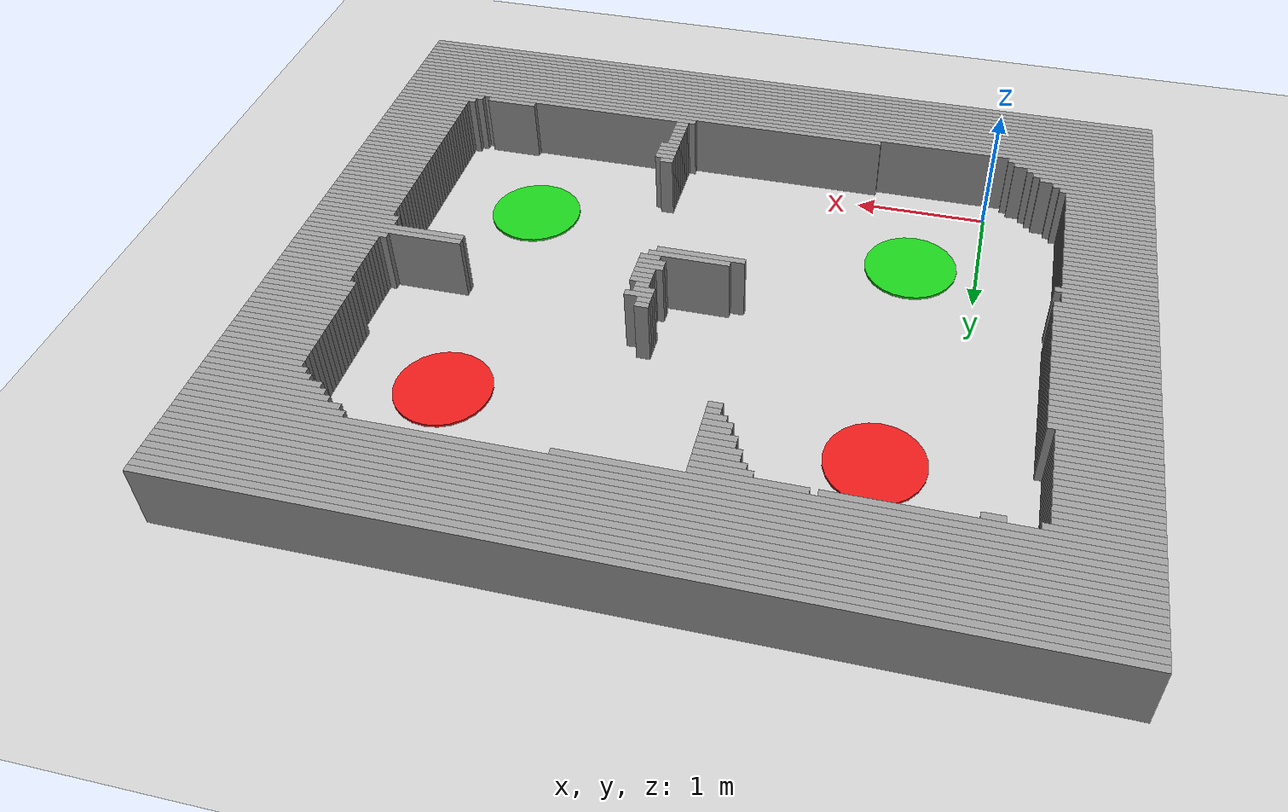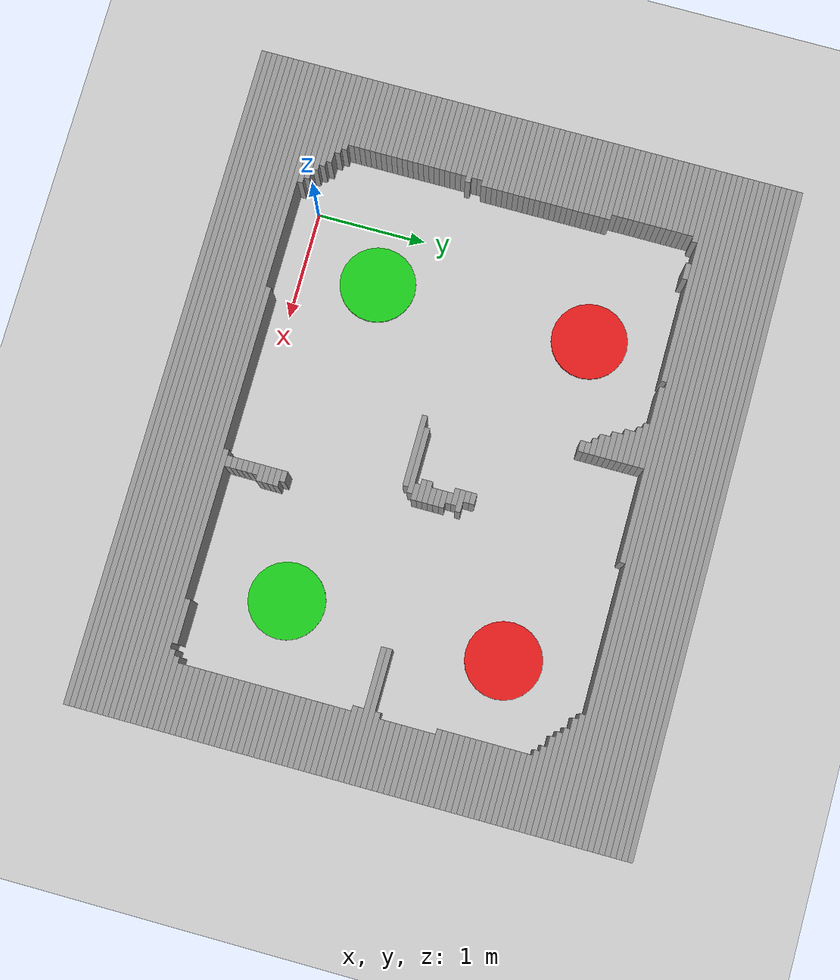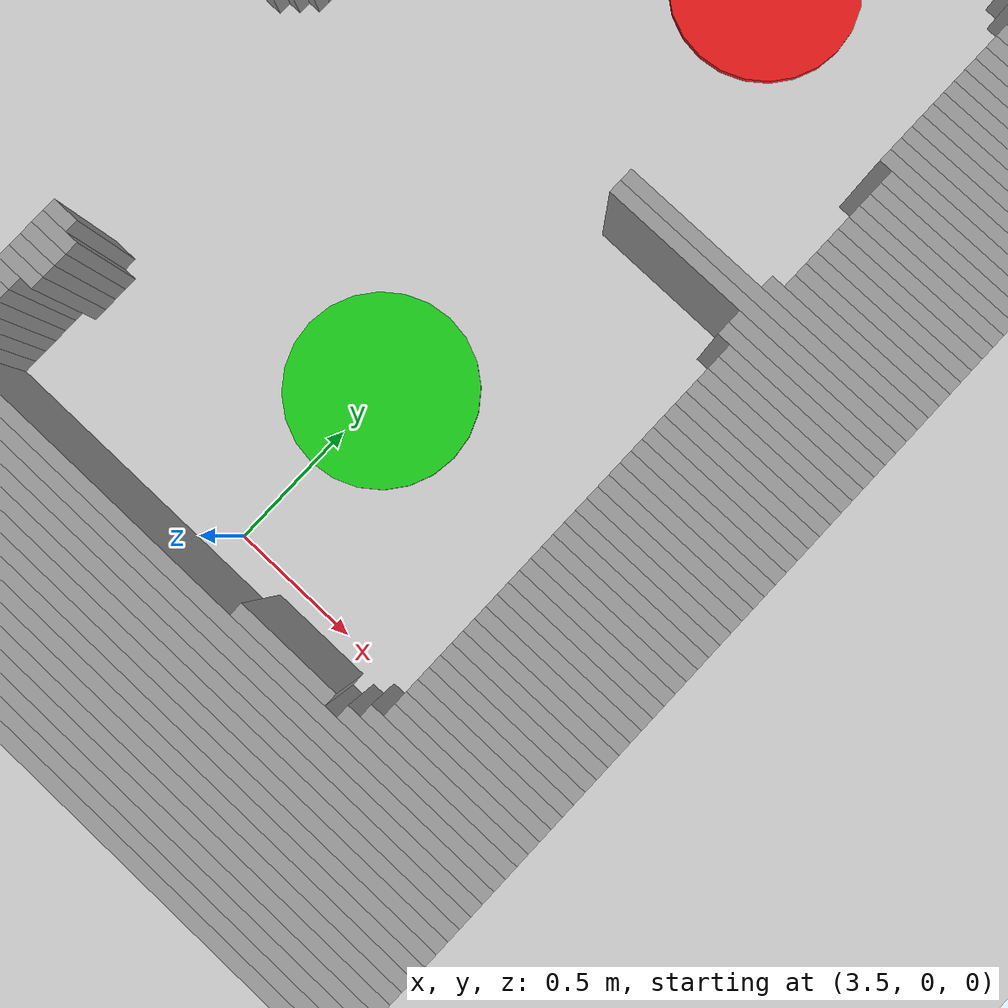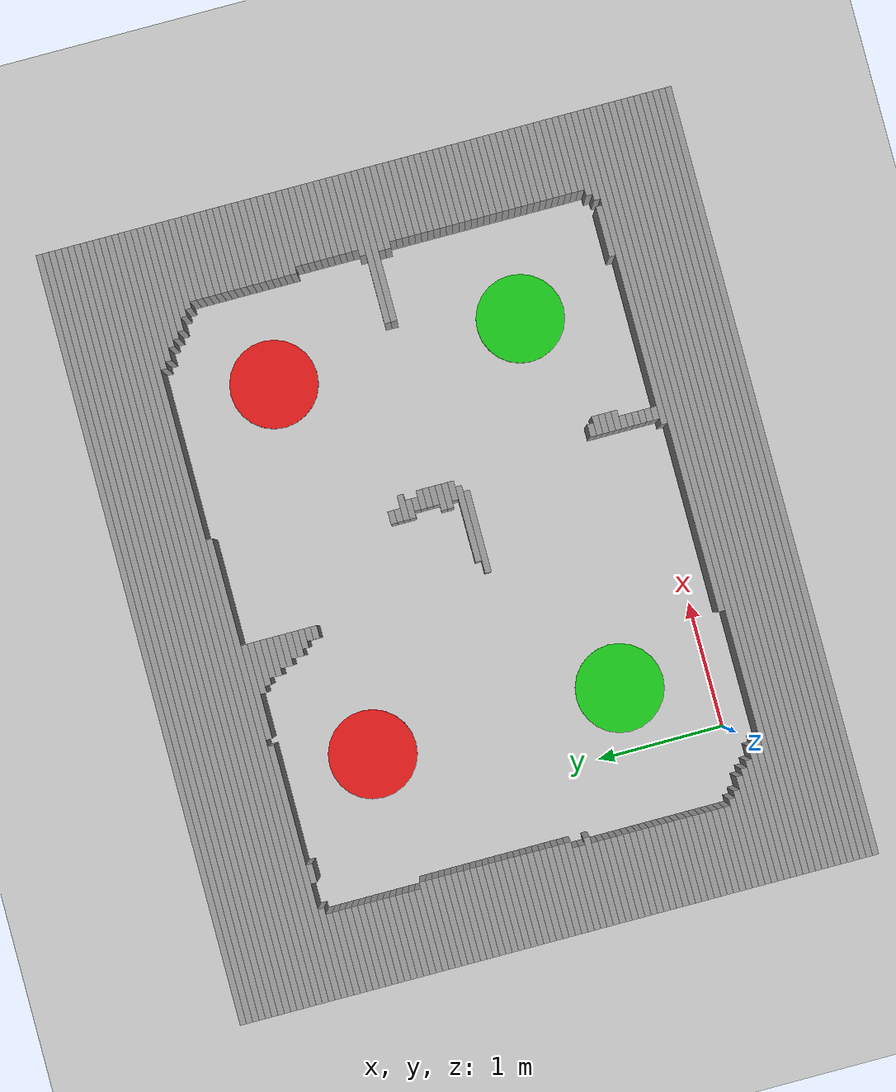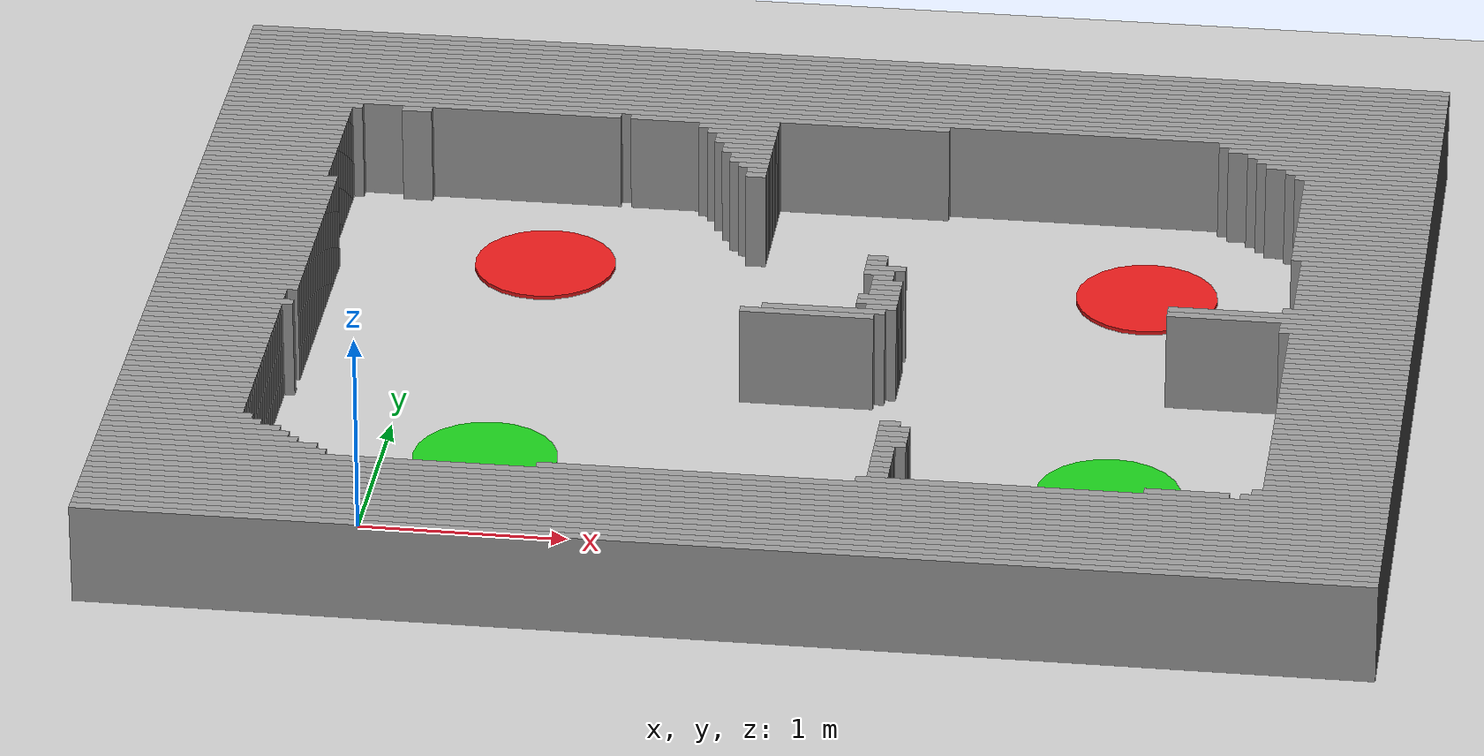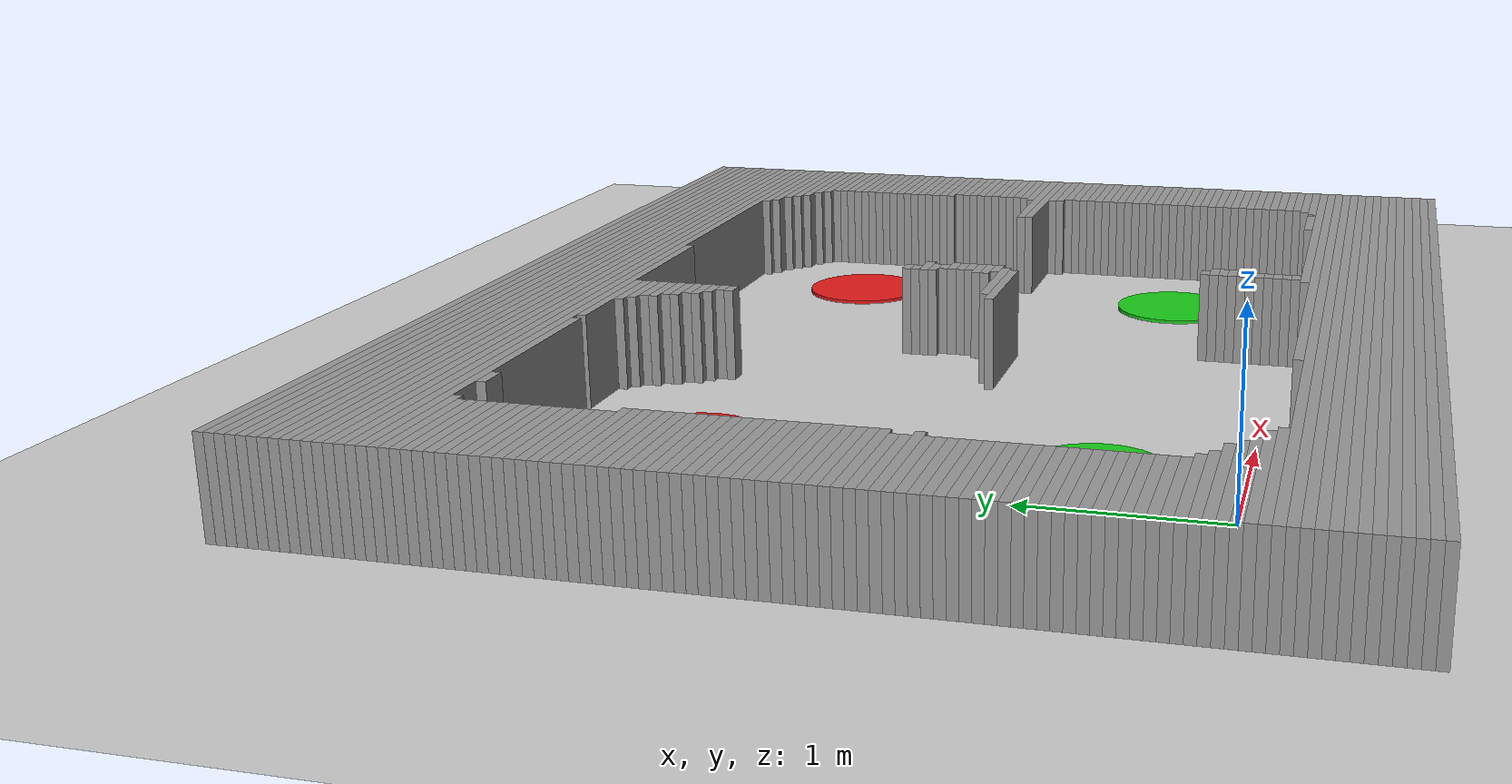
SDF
<?xml version="1.0" ?>
<sdf version="1.6">
  <world name="lab_world">

    <plugin filename="gz-sim-physics-system"
            name="gz::sim::systems::Physics"/>
    <plugin filename="gz-sim-user-commands-system"
            name="gz::sim::systems::UserCommands"/>
    <plugin filename="gz-sim-scene-broadcaster-system"
            name="gz::sim::systems::SceneBroadcaster"/>
    <plugin filename="gz-sim-sensors-system"
            name="gz::sim::systems::Sensors">
      <render_engine>ogre2</render_engine>
    </plugin>
    <plugin filename="gz-sim-imu-system"
            name="gz::sim::systems::Imu"/>

    <light name="sun" type="directional">
      <cast_shadows>true</cast_shadows>
      <pose>0 0 10 0 0 0</pose>
      <diffuse>0.8 0.8 0.8 1</diffuse>
      <specular>0.2 0.2 0.2 1</specular>
      <direction>-0.5 0.1 -0.9</direction>
    </light>

    <model name="ground_plane">
      <static>true</static>
      <link name="link">
        <collision name="collision">
          <geometry><plane><normal>0 0 1</normal><size>100 100</size></plane></geometry>
        </collision>
        <visual name="visual">
          <geometry><plane><normal>0 0 1</normal><size>100 100</size></plane></geometry>
          <material><ambient>0.8 0.8 0.8 1</ambient><diffuse>0.8 0.8 0.8 1</diffuse></material>
        </visual>
      </link>
    </model>

    <model name='wall_0'>
      <static>true</static>
      <pose>1.8340 4.1660 0.2500 0 0 0</pose>
      <link name='link'>
        <collision name='col'><geometry><box><size>6.1000 0.0500 0.5000</size></box></geometry></collision>
        <visual name='vis'>
          <geometry><box><size>6.1000 0.0500 0.5000</size></box></geometry>
          <material><ambient>0.4 0.4 0.4 1</ambient><diffuse>0.6 0.6 0.6 1</diffuse></material>
        </visual>
      </link>
    </model>
    <model name='wall_1'>
      <static>true</static>
      <pose>1.8340 4.1160 0.2500 0 0 0</pose>
      <link name='link'>
        <collision name='col'><geometry><box><size>6.1000 0.0500 0.5000</size></box></geometry></collision>
        <visual name='vis'>
          <geometry><box><size>6.1000 0.0500 0.5000</size></box></geometry>
          <material><ambient>0.4 0.4 0.4 1</ambient><diffuse>0.6 0.6 0.6 1</diffuse></material>
        </visual>
      </link>
    </model>
    <model name='wall_2'>
      <static>true</static>
      <pose>1.8340 4.0660 0.2500 0 0 0</pose>
      <link name='link'>
        <collision name='col'><geometry><box><size>6.1000 0.0500 0.5000</size></box></geometry></collision>
        <visual name='vis'>
          <geometry><box><size>6.1000 0.0500 0.5000</size></box></geometry>
          <material><ambient>0.4 0.4 0.4 1</ambient><diffuse>0.6 0.6 0.6 1</diffuse></material>
        </visual>
      </link>
    </model>
    <model name='wall_3'>
      <static>true</static>
      <pose>1.8340 4.0160 0.2500 0 0 0</pose>
      <link name='link'>
        <collision name='col'><geometry><box><size>6.1000 0.0500 0.5000</size></box></geometry></collision>
        <visual name='vis'>
          <geometry><box><size>6.1000 0.0500 0.5000</size></box></geometry>
          <material><ambient>0.4 0.4 0.4 1</ambient><diffuse>0.6 0.6 0.6 1</diffuse></material>
        </visual>
      </link>
    </model>
    <model name='wall_4'>
      <static>true</static>
      <pose>1.8340 3.9660 0.2500 0 0 0</pose>
      <link name='link'>
        <collision name='col'><geometry><box><size>6.1000 0.0500 0.5000</size></box></geometry></collision>
        <visual name='vis'>
          <geometry><box><size>6.1000 0.0500 0.5000</size></box></geometry>
          <material><ambient>0.4 0.4 0.4 1</ambient><diffuse>0.6 0.6 0.6 1</diffuse></material>
        </visual>
      </link>
    </model>
    <model name='wall_5'>
      <static>true</static>
      <pose>1.8340 3.9160 0.2500 0 0 0</pose>
      <link name='link'>
        <collision name='col'><geometry><box><size>6.1000 0.0500 0.5000</size></box></geometry></collision>
        <visual name='vis'>
          <geometry><box><size>6.1000 0.0500 0.5000</size></box></geometry>
          <material><ambient>0.4 0.4 0.4 1</ambient><diffuse>0.6 0.6 0.6 1</diffuse></material>
        </visual>
      </link>
    </model>
    <model name='wall_6'>
      <static>true</static>
      <pose>1.8340 3.8660 0.2500 0 0 0</pose>
      <link name='link'>
        <collision name='col'><geometry><box><size>6.1000 0.0500 0.5000</size></box></geometry></collision>
        <visual name='vis'>
          <geometry><box><size>6.1000 0.0500 0.5000</size></box></geometry>
          <material><ambient>0.4 0.4 0.4 1</ambient><diffuse>0.6 0.6 0.6 1</diffuse></material>
        </visual>
      </link>
    </model>
    <model name='wall_7'>
      <static>true</static>
      <pose>1.8340 3.8160 0.2500 0 0 0</pose>
      <link name='link'>
        <collision name='col'><geometry><box><size>6.1000 0.0500 0.5000</size></box></geometry></collision>
        <visual name='vis'>
          <geometry><box><size>6.1000 0.0500 0.5000</size></box></geometry>
          <material><ambient>0.4 0.4 0.4 1</ambient><diffuse>0.6 0.6 0.6 1</diffuse></material>
        </visual>
      </link>
    </model>
    <model name='wall_8'>
      <static>true</static>
      <pose>1.8340 3.7660 0.2500 0 0 0</pose>
      <link name='link'>
        <collision name='col'><geometry><box><size>6.1000 0.0500 0.5000</size></box></geometry></collision>
        <visual name='vis'>
          <geometry><box><size>6.1000 0.0500 0.5000</size></box></geometry>
          <material><ambient>0.4 0.4 0.4 1</ambient><diffuse>0.6 0.6 0.6 1</diffuse></material>
        </visual>
      </link>
    </model>
    <model name='wall_9'>
      <static>true</static>
      <pose>1.8340 3.7160 0.2500 0 0 0</pose>
      <link name='link'>
        <collision name='col'><geometry><box><size>6.1000 0.0500 0.5000</size></box></geometry></collision>
        <visual name='vis'>
          <geometry><box><size>6.1000 0.0500 0.5000</size></box></geometry>
          <material><ambient>0.4 0.4 0.4 1</ambient><diffuse>0.6 0.6 0.6 1</diffuse></material>
        </visual>
      </link>
    </model>
    <model name='wall_10'>
      <static>true</static>
      <pose>1.8340 3.6660 0.2500 0 0 0</pose>
      <link name='link'>
        <collision name='col'><geometry><box><size>6.1000 0.0500 0.5000</size></box></geometry></collision>
        <visual name='vis'>
          <geometry><box><size>6.1000 0.0500 0.5000</size></box></geometry>
          <material><ambient>0.4 0.4 0.4 1</ambient><diffuse>0.6 0.6 0.6 1</diffuse></material>
        </visual>
      </link>
    </model>
    <model name='wall_11'>
      <static>true</static>
      <pose>1.8340 3.6160 0.2500 0 0 0</pose>
      <link name='link'>
        <collision name='col'><geometry><box><size>6.1000 0.0500 0.5000</size></box></geometry></collision>
        <visual name='vis'>
          <geometry><box><size>6.1000 0.0500 0.5000</size></box></geometry>
          <material><ambient>0.4 0.4 0.4 1</ambient><diffuse>0.6 0.6 0.6 1</diffuse></material>
        </visual>
      </link>
    </model>
    <model name='wall_12'>
      <static>true</static>
      <pose>1.8340 3.5660 0.2500 0 0 0</pose>
      <link name='link'>
        <collision name='col'><geometry><box><size>6.1000 0.0500 0.5000</size></box></geometry></collision>
        <visual name='vis'>
          <geometry><box><size>6.1000 0.0500 0.5000</size></box></geometry>
          <material><ambient>0.4 0.4 0.4 1</ambient><diffuse>0.6 0.6 0.6 1</diffuse></material>
        </visual>
      </link>
    </model>
    <model name='wall_13'>
      <static>true</static>
      <pose>1.8340 3.5160 0.2500 0 0 0</pose>
      <link name='link'>
        <collision name='col'><geometry><box><size>6.1000 0.0500 0.5000</size></box></geometry></collision>
        <visual name='vis'>
          <geometry><box><size>6.1000 0.0500 0.5000</size></box></geometry>
          <material><ambient>0.4 0.4 0.4 1</ambient><diffuse>0.6 0.6 0.6 1</diffuse></material>
        </visual>
      </link>
    </model>
    <model name='wall_14'>
      <static>true</static>
      <pose>0.6090 3.4660 0.2500 0 0 0</pose>
      <link name='link'>
        <collision name='col'><geometry><box><size>3.6500 0.0500 0.5000</size></box></geometry></collision>
        <visual name='vis'>
          <geometry><box><size>3.6500 0.0500 0.5000</size></box></geometry>
          <material><ambient>0.4 0.4 0.4 1</ambient><diffuse>0.6 0.6 0.6 1</diffuse></material>
        </visual>
      </link>
    </model>
    <model name='wall_15'>
      <static>true</static>
      <pose>4.3340 3.4660 0.2500 0 0 0</pose>
      <link name='link'>
        <collision name='col'><geometry><box><size>1.1000 0.0500 0.5000</size></box></geometry></collision>
        <visual name='vis'>
          <geometry><box><size>1.1000 0.0500 0.5000</size></box></geometry>
          <material><ambient>0.4 0.4 0.4 1</ambient><diffuse>0.6 0.6 0.6 1</diffuse></material>
        </visual>
      </link>
    </model>
    <model name='wall_16'>
      <static>true</static>
      <pose>-0.2160 3.4160 0.2500 0 0 0</pose>
      <link name='link'>
        <collision name='col'><geometry><box><size>2.0000 0.0500 0.5000</size></box></geometry></collision>
        <visual name='vis'>
          <geometry><box><size>2.0000 0.0500 0.5000</size></box></geometry>
          <material><ambient>0.4 0.4 0.4 1</ambient><diffuse>0.6 0.6 0.6 1</diffuse></material>
        </visual>
      </link>
    </model>
    <model name='wall_17'>
      <static>true</static>
      <pose>1.2090 3.4160 0.2500 0 0 0</pose>
      <link name='link'>
        <collision name='col'><geometry><box><size>0.7500 0.0500 0.5000</size></box></geometry></collision>
        <visual name='vis'>
          <geometry><box><size>0.7500 0.0500 0.5000</size></box></geometry>
          <material><ambient>0.4 0.4 0.4 1</ambient><diffuse>0.6 0.6 0.6 1</diffuse></material>
        </visual>
      </link>
    </model>
    <model name='wall_18'>
      <static>true</static>
      <pose>4.3590 3.4160 0.2500 0 0 0</pose>
      <link name='link'>
        <collision name='col'><geometry><box><size>1.0500 0.0500 0.5000</size></box></geometry></collision>
        <visual name='vis'>
          <geometry><box><size>1.0500 0.0500 0.5000</size></box></geometry>
          <material><ambient>0.4 0.4 0.4 1</ambient><diffuse>0.6 0.6 0.6 1</diffuse></material>
        </visual>
      </link>
    </model>
    <model name='wall_19'>
      <static>true</static>
      <pose>-0.8660 3.3660 0.2500 0 0 0</pose>
      <link name='link'>
        <collision name='col'><geometry><box><size>0.7000 0.0500 0.5000</size></box></geometry></collision>
        <visual name='vis'>
          <geometry><box><size>0.7000 0.0500 0.5000</size></box></geometry>
          <material><ambient>0.4 0.4 0.4 1</ambient><diffuse>0.6 0.6 0.6 1</diffuse></material>
        </visual>
      </link>
    </model>
    <model name='wall_20'>
      <static>true</static>
      <pose>-0.2410 3.3660 0.2500 0 0 0</pose>
      <link name='link'>
        <collision name='col'><geometry><box><size>0.1500 0.0500 0.5000</size></box></geometry></collision>
        <visual name='vis'>
          <geometry><box><size>0.1500 0.0500 0.5000</size></box></geometry>
          <material><ambient>0.4 0.4 0.4 1</ambient><diffuse>0.6 0.6 0.6 1</diffuse></material>
        </visual>
      </link>
    </model>
    <model name='wall_21'>
      <static>true</static>
      <pose>1.3840 3.3660 0.2500 0 0 0</pose>
      <link name='link'>
        <collision name='col'><geometry><box><size>0.4000 0.0500 0.5000</size></box></geometry></collision>
        <visual name='vis'>
          <geometry><box><size>0.4000 0.0500 0.5000</size></box></geometry>
          <material><ambient>0.4 0.4 0.4 1</ambient><diffuse>0.6 0.6 0.6 1</diffuse></material>
        </visual>
      </link>
    </model>
    <model name='wall_22'>
      <static>true</static>
      <pose>4.4090 3.3660 0.2500 0 0 0</pose>
      <link name='link'>
        <collision name='col'><geometry><box><size>0.9500 0.0500 0.5000</size></box></geometry></collision>
        <visual name='vis'>
          <geometry><box><size>0.9500 0.0500 0.5000</size></box></geometry>
          <material><ambient>0.4 0.4 0.4 1</ambient><diffuse>0.6 0.6 0.6 1</diffuse></material>
        </visual>
      </link>
    </model>
    <model name='wall_23'>
      <static>true</static>
      <pose>-0.8910 3.3160 0.2500 0 0 0</pose>
      <link name='link'>
        <collision name='col'><geometry><box><size>0.6500 0.0500 0.5000</size></box></geometry></collision>
        <visual name='vis'>
          <geometry><box><size>0.6500 0.0500 0.5000</size></box></geometry>
          <material><ambient>0.4 0.4 0.4 1</ambient><diffuse>0.6 0.6 0.6 1</diffuse></material>
        </visual>
      </link>
    </model>
    <model name='wall_24'>
      <static>true</static>
      <pose>1.4090 3.3160 0.2500 0 0 0</pose>
      <link name='link'>
        <collision name='col'><geometry><box><size>0.3500 0.0500 0.5000</size></box></geometry></collision>
        <visual name='vis'>
          <geometry><box><size>0.3500 0.0500 0.5000</size></box></geometry>
          <material><ambient>0.4 0.4 0.4 1</ambient><diffuse>0.6 0.6 0.6 1</diffuse></material>
        </visual>
      </link>
    </model>
    <model name='wall_25'>
      <static>true</static>
      <pose>4.4340 3.3160 0.2500 0 0 0</pose>
      <link name='link'>
        <collision name='col'><geometry><box><size>0.9000 0.0500 0.5000</size></box></geometry></collision>
        <visual name='vis'>
          <geometry><box><size>0.9000 0.0500 0.5000</size></box></geometry>
          <material><ambient>0.4 0.4 0.4 1</ambient><diffuse>0.6 0.6 0.6 1</diffuse></material>
        </visual>
      </link>
    </model>
    <model name='wall_26'>
      <static>true</static>
      <pose>-0.8910 3.2660 0.2500 0 0 0</pose>
      <link name='link'>
        <collision name='col'><geometry><box><size>0.6500 0.0500 0.5000</size></box></geometry></collision>
        <visual name='vis'>
          <geometry><box><size>0.6500 0.0500 0.5000</size></box></geometry>
          <material><ambient>0.4 0.4 0.4 1</ambient><diffuse>0.6 0.6 0.6 1</diffuse></material>
        </visual>
      </link>
    </model>
    <model name='wall_27'>
      <static>true</static>
      <pose>1.4340 3.2660 0.2500 0 0 0</pose>
      <link name='link'>
        <collision name='col'><geometry><box><size>0.3000 0.0500 0.5000</size></box></geometry></collision>
        <visual name='vis'>
          <geometry><box><size>0.3000 0.0500 0.5000</size></box></geometry>
          <material><ambient>0.4 0.4 0.4 1</ambient><diffuse>0.6 0.6 0.6 1</diffuse></material>
        </visual>
      </link>
    </model>
    <model name='wall_28'>
      <static>true</static>
      <pose>4.4590 3.2660 0.2500 0 0 0</pose>
      <link name='link'>
        <collision name='col'><geometry><box><size>0.8500 0.0500 0.5000</size></box></geometry></collision>
        <visual name='vis'>
          <geometry><box><size>0.8500 0.0500 0.5000</size></box></geometry>
          <material><ambient>0.4 0.4 0.4 1</ambient><diffuse>0.6 0.6 0.6 1</diffuse></material>
        </visual>
      </link>
    </model>
    <model name='wall_29'>
      <static>true</static>
      <pose>-0.8910 3.2160 0.2500 0 0 0</pose>
      <link name='link'>
        <collision name='col'><geometry><box><size>0.6500 0.0500 0.5000</size></box></geometry></collision>
        <visual name='vis'>
          <geometry><box><size>0.6500 0.0500 0.5000</size></box></geometry>
          <material><ambient>0.4 0.4 0.4 1</ambient><diffuse>0.6 0.6 0.6 1</diffuse></material>
        </visual>
      </link>
    </model>
    <model name='wall_30'>
      <static>true</static>
      <pose>1.4340 3.2160 0.2500 0 0 0</pose>
      <link name='link'>
        <collision name='col'><geometry><box><size>0.3000 0.0500 0.5000</size></box></geometry></collision>
        <visual name='vis'>
          <geometry><box><size>0.3000 0.0500 0.5000</size></box></geometry>
          <material><ambient>0.4 0.4 0.4 1</ambient><diffuse>0.6 0.6 0.6 1</diffuse></material>
        </visual>
      </link>
    </model>
    <model name='wall_31'>
      <static>true</static>
      <pose>4.5090 3.2160 0.2500 0 0 0</pose>
      <link name='link'>
        <collision name='col'><geometry><box><size>0.7500 0.0500 0.5000</size></box></geometry></collision>
        <visual name='vis'>
          <geometry><box><size>0.7500 0.0500 0.5000</size></box></geometry>
          <material><ambient>0.4 0.4 0.4 1</ambient><diffuse>0.6 0.6 0.6 1</diffuse></material>
        </visual>
      </link>
    </model>
    <model name='wall_32'>
      <static>true</static>
      <pose>-0.8910 3.1660 0.2500 0 0 0</pose>
      <link name='link'>
        <collision name='col'><geometry><box><size>0.6500 0.0500 0.5000</size></box></geometry></collision>
        <visual name='vis'>
          <geometry><box><size>0.6500 0.0500 0.5000</size></box></geometry>
          <material><ambient>0.4 0.4 0.4 1</ambient><diffuse>0.6 0.6 0.6 1</diffuse></material>
        </visual>
      </link>
    </model>
    <model name='wall_33'>
      <static>true</static>
      <pose>1.4590 3.1660 0.2500 0 0 0</pose>
      <link name='link'>
        <collision name='col'><geometry><box><size>0.2500 0.0500 0.5000</size></box></geometry></collision>
        <visual name='vis'>
          <geometry><box><size>0.2500 0.0500 0.5000</size></box></geometry>
          <material><ambient>0.4 0.4 0.4 1</ambient><diffuse>0.6 0.6 0.6 1</diffuse></material>
        </visual>
      </link>
    </model>
    <model name='wall_34'>
      <static>true</static>
      <pose>4.5340 3.1660 0.2500 0 0 0</pose>
      <link name='link'>
        <collision name='col'><geometry><box><size>0.7000 0.0500 0.5000</size></box></geometry></collision>
        <visual name='vis'>
          <geometry><box><size>0.7000 0.0500 0.5000</size></box></geometry>
          <material><ambient>0.4 0.4 0.4 1</ambient><diffuse>0.6 0.6 0.6 1</diffuse></material>
        </visual>
      </link>
    </model>
    <model name='wall_35'>
      <static>true</static>
      <pose>-0.8910 3.1160 0.2500 0 0 0</pose>
      <link name='link'>
        <collision name='col'><geometry><box><size>0.6500 0.0500 0.5000</size></box></geometry></collision>
        <visual name='vis'>
          <geometry><box><size>0.6500 0.0500 0.5000</size></box></geometry>
          <material><ambient>0.4 0.4 0.4 1</ambient><diffuse>0.6 0.6 0.6 1</diffuse></material>
        </visual>
      </link>
    </model>
    <model name='wall_36'>
      <static>true</static>
      <pose>1.4590 3.1160 0.2500 0 0 0</pose>
      <link name='link'>
        <collision name='col'><geometry><box><size>0.2500 0.0500 0.5000</size></box></geometry></collision>
        <visual name='vis'>
          <geometry><box><size>0.2500 0.0500 0.5000</size></box></geometry>
          <material><ambient>0.4 0.4 0.4 1</ambient><diffuse>0.6 0.6 0.6 1</diffuse></material>
        </visual>
      </link>
    </model>
    <model name='wall_37'>
      <static>true</static>
      <pose>4.5590 3.1160 0.2500 0 0 0</pose>
      <link name='link'>
        <collision name='col'><geometry><box><size>0.6500 0.0500 0.5000</size></box></geometry></collision>
        <visual name='vis'>
          <geometry><box><size>0.6500 0.0500 0.5000</size></box></geometry>
          <material><ambient>0.4 0.4 0.4 1</ambient><diffuse>0.6 0.6 0.6 1</diffuse></material>
        </visual>
      </link>
    </model>
    <model name='wall_38'>
      <static>true</static>
      <pose>-0.8910 3.0660 0.2500 0 0 0</pose>
      <link name='link'>
        <collision name='col'><geometry><box><size>0.6500 0.0500 0.5000</size></box></geometry></collision>
        <visual name='vis'>
          <geometry><box><size>0.6500 0.0500 0.5000</size></box></geometry>
          <material><ambient>0.4 0.4 0.4 1</ambient><diffuse>0.6 0.6 0.6 1</diffuse></material>
        </visual>
      </link>
    </model>
    <model name='wall_39'>
      <static>true</static>
      <pose>1.4840 3.0660 0.2500 0 0 0</pose>
      <link name='link'>
        <collision name='col'><geometry><box><size>0.2000 0.0500 0.5000</size></box></geometry></collision>
        <visual name='vis'>
          <geometry><box><size>0.2000 0.0500 0.5000</size></box></geometry>
          <material><ambient>0.4 0.4 0.4 1</ambient><diffuse>0.6 0.6 0.6 1</diffuse></material>
        </visual>
      </link>
    </model>
    <model name='wall_40'>
      <static>true</static>
      <pose>4.5590 3.0660 0.2500 0 0 0</pose>
      <link name='link'>
        <collision name='col'><geometry><box><size>0.6500 0.0500 0.5000</size></box></geometry></collision>
        <visual name='vis'>
          <geometry><box><size>0.6500 0.0500 0.5000</size></box></geometry>
          <material><ambient>0.4 0.4 0.4 1</ambient><diffuse>0.6 0.6 0.6 1</diffuse></material>
        </visual>
      </link>
    </model>
    <model name='wall_41'>
      <static>true</static>
      <pose>-0.8910 3.0160 0.2500 0 0 0</pose>
      <link name='link'>
        <collision name='col'><geometry><box><size>0.6500 0.0500 0.5000</size></box></geometry></collision>
        <visual name='vis'>
          <geometry><box><size>0.6500 0.0500 0.5000</size></box></geometry>
          <material><ambient>0.4 0.4 0.4 1</ambient><diffuse>0.6 0.6 0.6 1</diffuse></material>
        </visual>
      </link>
    </model>
    <model name='wall_42'>
      <static>true</static>
      <pose>1.4840 3.0160 0.2500 0 0 0</pose>
      <link name='link'>
        <collision name='col'><geometry><box><size>0.2000 0.0500 0.5000</size></box></geometry></collision>
        <visual name='vis'>
          <geometry><box><size>0.2000 0.0500 0.5000</size></box></geometry>
          <material><ambient>0.4 0.4 0.4 1</ambient><diffuse>0.6 0.6 0.6 1</diffuse></material>
        </visual>
      </link>
    </model>
    <model name='wall_43'>
      <static>true</static>
      <pose>4.5590 3.0160 0.2500 0 0 0</pose>
      <link name='link'>
        <collision name='col'><geometry><box><size>0.6500 0.0500 0.5000</size></box></geometry></collision>
        <visual name='vis'>
          <geometry><box><size>0.6500 0.0500 0.5000</size></box></geometry>
          <material><ambient>0.4 0.4 0.4 1</ambient><diffuse>0.6 0.6 0.6 1</diffuse></material>
        </visual>
      </link>
    </model>
    <model name='wall_44'>
      <static>true</static>
      <pose>-0.8910 2.9660 0.2500 0 0 0</pose>
      <link name='link'>
        <collision name='col'><geometry><box><size>0.6500 0.0500 0.5000</size></box></geometry></collision>
        <visual name='vis'>
          <geometry><box><size>0.6500 0.0500 0.5000</size></box></geometry>
          <material><ambient>0.4 0.4 0.4 1</ambient><diffuse>0.6 0.6 0.6 1</diffuse></material>
        </visual>
      </link>
    </model>
    <model name='wall_45'>
      <static>true</static>
      <pose>1.5090 2.9660 0.2500 0 0 0</pose>
      <link name='link'>
        <collision name='col'><geometry><box><size>0.1500 0.0500 0.5000</size></box></geometry></collision>
        <visual name='vis'>
          <geometry><box><size>0.1500 0.0500 0.5000</size></box></geometry>
          <material><ambient>0.4 0.4 0.4 1</ambient><diffuse>0.6 0.6 0.6 1</diffuse></material>
        </visual>
      </link>
    </model>
    <model name='wall_46'>
      <static>true</static>
      <pose>4.5590 2.9660 0.2500 0 0 0</pose>
      <link name='link'>
        <collision name='col'><geometry><box><size>0.6500 0.0500 0.5000</size></box></geometry></collision>
        <visual name='vis'>
          <geometry><box><size>0.6500 0.0500 0.5000</size></box></geometry>
          <material><ambient>0.4 0.4 0.4 1</ambient><diffuse>0.6 0.6 0.6 1</diffuse></material>
        </visual>
      </link>
    </model>
    <model name='wall_47'>
      <static>true</static>
      <pose>-0.8910 2.9160 0.2500 0 0 0</pose>
      <link name='link'>
        <collision name='col'><geometry><box><size>0.6500 0.0500 0.5000</size></box></geometry></collision>
        <visual name='vis'>
          <geometry><box><size>0.6500 0.0500 0.5000</size></box></geometry>
          <material><ambient>0.4 0.4 0.4 1</ambient><diffuse>0.6 0.6 0.6 1</diffuse></material>
        </visual>
      </link>
    </model>
    <model name='wall_48'>
      <static>true</static>
      <pose>1.5340 2.9160 0.2500 0 0 0</pose>
      <link name='link'>
        <collision name='col'><geometry><box><size>0.1000 0.0500 0.5000</size></box></geometry></collision>
        <visual name='vis'>
          <geometry><box><size>0.1000 0.0500 0.5000</size></box></geometry>
          <material><ambient>0.4 0.4 0.4 1</ambient><diffuse>0.6 0.6 0.6 1</diffuse></material>
        </visual>
      </link>
    </model>
    <model name='wall_49'>
      <static>true</static>
      <pose>4.5590 2.9160 0.2500 0 0 0</pose>
      <link name='link'>
        <collision name='col'><geometry><box><size>0.6500 0.0500 0.5000</size></box></geometry></collision>
        <visual name='vis'>
          <geometry><box><size>0.6500 0.0500 0.5000</size></box></geometry>
          <material><ambient>0.4 0.4 0.4 1</ambient><diffuse>0.6 0.6 0.6 1</diffuse></material>
        </visual>
      </link>
    </model>
    <model name='wall_50'>
      <static>true</static>
      <pose>-0.8910 2.8660 0.2500 0 0 0</pose>
      <link name='link'>
        <collision name='col'><geometry><box><size>0.6500 0.0500 0.5000</size></box></geometry></collision>
        <visual name='vis'>
          <geometry><box><size>0.6500 0.0500 0.5000</size></box></geometry>
          <material><ambient>0.4 0.4 0.4 1</ambient><diffuse>0.6 0.6 0.6 1</diffuse></material>
        </visual>
      </link>
    </model>
    <model name='wall_51'>
      <static>true</static>
      <pose>1.5340 2.8660 0.2500 0 0 0</pose>
      <link name='link'>
        <collision name='col'><geometry><box><size>0.1000 0.0500 0.5000</size></box></geometry></collision>
        <visual name='vis'>
          <geometry><box><size>0.1000 0.0500 0.5000</size></box></geometry>
          <material><ambient>0.4 0.4 0.4 1</ambient><diffuse>0.6 0.6 0.6 1</diffuse></material>
        </visual>
      </link>
    </model>
    <model name='wall_52'>
      <static>true</static>
      <pose>4.5590 2.8660 0.2500 0 0 0</pose>
      <link name='link'>
        <collision name='col'><geometry><box><size>0.6500 0.0500 0.5000</size></box></geometry></collision>
        <visual name='vis'>
          <geometry><box><size>0.6500 0.0500 0.5000</size></box></geometry>
          <material><ambient>0.4 0.4 0.4 1</ambient><diffuse>0.6 0.6 0.6 1</diffuse></material>
        </visual>
      </link>
    </model>
    <model name='wall_53'>
      <static>true</static>
      <pose>-0.8910 2.8160 0.2500 0 0 0</pose>
      <link name='link'>
        <collision name='col'><geometry><box><size>0.6500 0.0500 0.5000</size></box></geometry></collision>
        <visual name='vis'>
          <geometry><box><size>0.6500 0.0500 0.5000</size></box></geometry>
          <material><ambient>0.4 0.4 0.4 1</ambient><diffuse>0.6 0.6 0.6 1</diffuse></material>
        </visual>
      </link>
    </model>
    <model name='wall_54'>
      <static>true</static>
      <pose>4.5590 2.8160 0.2500 0 0 0</pose>
      <link name='link'>
        <collision name='col'><geometry><box><size>0.6500 0.0500 0.5000</size></box></geometry></collision>
        <visual name='vis'>
          <geometry><box><size>0.6500 0.0500 0.5000</size></box></geometry>
          <material><ambient>0.4 0.4 0.4 1</ambient><diffuse>0.6 0.6 0.6 1</diffuse></material>
        </visual>
      </link>
    </model>
    <model name='wall_55'>
      <static>true</static>
      <pose>-0.8910 2.7660 0.2500 0 0 0</pose>
      <link name='link'>
        <collision name='col'><geometry><box><size>0.6500 0.0500 0.5000</size></box></geometry></collision>
        <visual name='vis'>
          <geometry><box><size>0.6500 0.0500 0.5000</size></box></geometry>
          <material><ambient>0.4 0.4 0.4 1</ambient><diffuse>0.6 0.6 0.6 1</diffuse></material>
        </visual>
      </link>
    </model>
    <model name='wall_56'>
      <static>true</static>
      <pose>4.5590 2.7660 0.2500 0 0 0</pose>
      <link name='link'>
        <collision name='col'><geometry><box><size>0.6500 0.0500 0.5000</size></box></geometry></collision>
        <visual name='vis'>
          <geometry><box><size>0.6500 0.0500 0.5000</size></box></geometry>
          <material><ambient>0.4 0.4 0.4 1</ambient><diffuse>0.6 0.6 0.6 1</diffuse></material>
        </visual>
      </link>
    </model>
    <model name='wall_57'>
      <static>true</static>
      <pose>-0.8910 2.7160 0.2500 0 0 0</pose>
      <link name='link'>
        <collision name='col'><geometry><box><size>0.6500 0.0500 0.5000</size></box></geometry></collision>
        <visual name='vis'>
          <geometry><box><size>0.6500 0.0500 0.5000</size></box></geometry>
          <material><ambient>0.4 0.4 0.4 1</ambient><diffuse>0.6 0.6 0.6 1</diffuse></material>
        </visual>
      </link>
    </model>
    <model name='wall_58'>
      <static>true</static>
      <pose>4.5590 2.7160 0.2500 0 0 0</pose>
      <link name='link'>
        <collision name='col'><geometry><box><size>0.6500 0.0500 0.5000</size></box></geometry></collision>
        <visual name='vis'>
          <geometry><box><size>0.6500 0.0500 0.5000</size></box></geometry>
          <material><ambient>0.4 0.4 0.4 1</ambient><diffuse>0.6 0.6 0.6 1</diffuse></material>
        </visual>
      </link>
    </model>
    <model name='wall_59'>
      <static>true</static>
      <pose>-0.8910 2.6660 0.2500 0 0 0</pose>
      <link name='link'>
        <collision name='col'><geometry><box><size>0.6500 0.0500 0.5000</size></box></geometry></collision>
        <visual name='vis'>
          <geometry><box><size>0.6500 0.0500 0.5000</size></box></geometry>
          <material><ambient>0.4 0.4 0.4 1</ambient><diffuse>0.6 0.6 0.6 1</diffuse></material>
        </visual>
      </link>
    </model>
    <model name='wall_60'>
      <static>true</static>
      <pose>4.5590 2.6660 0.2500 0 0 0</pose>
      <link name='link'>
        <collision name='col'><geometry><box><size>0.6500 0.0500 0.5000</size></box></geometry></collision>
        <visual name='vis'>
          <geometry><box><size>0.6500 0.0500 0.5000</size></box></geometry>
          <material><ambient>0.4 0.4 0.4 1</ambient><diffuse>0.6 0.6 0.6 1</diffuse></material>
        </visual>
      </link>
    </model>
    <model name='wall_61'>
      <static>true</static>
      <pose>-0.8910 2.6160 0.2500 0 0 0</pose>
      <link name='link'>
        <collision name='col'><geometry><box><size>0.6500 0.0500 0.5000</size></box></geometry></collision>
        <visual name='vis'>
          <geometry><box><size>0.6500 0.0500 0.5000</size></box></geometry>
          <material><ambient>0.4 0.4 0.4 1</ambient><diffuse>0.6 0.6 0.6 1</diffuse></material>
        </visual>
      </link>
    </model>
    <model name='wall_62'>
      <static>true</static>
      <pose>4.5590 2.6160 0.2500 0 0 0</pose>
      <link name='link'>
        <collision name='col'><geometry><box><size>0.6500 0.0500 0.5000</size></box></geometry></collision>
        <visual name='vis'>
          <geometry><box><size>0.6500 0.0500 0.5000</size></box></geometry>
          <material><ambient>0.4 0.4 0.4 1</ambient><diffuse>0.6 0.6 0.6 1</diffuse></material>
        </visual>
      </link>
    </model>
    <model name='wall_63'>
      <static>true</static>
      <pose>-0.8660 2.5660 0.2500 0 0 0</pose>
      <link name='link'>
        <collision name='col'><geometry><box><size>0.7000 0.0500 0.5000</size></box></geometry></collision>
        <visual name='vis'>
          <geometry><box><size>0.7000 0.0500 0.5000</size></box></geometry>
          <material><ambient>0.4 0.4 0.4 1</ambient><diffuse>0.6 0.6 0.6 1</diffuse></material>
        </visual>
      </link>
    </model>
    <model name='wall_64'>
      <static>true</static>
      <pose>4.5590 2.5660 0.2500 0 0 0</pose>
      <link name='link'>
        <collision name='col'><geometry><box><size>0.6500 0.0500 0.5000</size></box></geometry></collision>
        <visual name='vis'>
          <geometry><box><size>0.6500 0.0500 0.5000</size></box></geometry>
          <material><ambient>0.4 0.4 0.4 1</ambient><diffuse>0.6 0.6 0.6 1</diffuse></material>
        </visual>
      </link>
    </model>
    <model name='wall_65'>
      <static>true</static>
      <pose>-0.8660 2.5160 0.2500 0 0 0</pose>
      <link name='link'>
        <collision name='col'><geometry><box><size>0.7000 0.0500 0.5000</size></box></geometry></collision>
        <visual name='vis'>
          <geometry><box><size>0.7000 0.0500 0.5000</size></box></geometry>
          <material><ambient>0.4 0.4 0.4 1</ambient><diffuse>0.6 0.6 0.6 1</diffuse></material>
        </visual>
      </link>
    </model>
    <model name='wall_66'>
      <static>true</static>
      <pose>4.5590 2.5160 0.2500 0 0 0</pose>
      <link name='link'>
        <collision name='col'><geometry><box><size>0.6500 0.0500 0.5000</size></box></geometry></collision>
        <visual name='vis'>
          <geometry><box><size>0.6500 0.0500 0.5000</size></box></geometry>
          <material><ambient>0.4 0.4 0.4 1</ambient><diffuse>0.6 0.6 0.6 1</diffuse></material>
        </visual>
      </link>
    </model>
    <model name='wall_67'>
      <static>true</static>
      <pose>-0.8660 2.4660 0.2500 0 0 0</pose>
      <link name='link'>
        <collision name='col'><geometry><box><size>0.7000 0.0500 0.5000</size></box></geometry></collision>
        <visual name='vis'>
          <geometry><box><size>0.7000 0.0500 0.5000</size></box></geometry>
          <material><ambient>0.4 0.4 0.4 1</ambient><diffuse>0.6 0.6 0.6 1</diffuse></material>
        </visual>
      </link>
    </model>
    <model name='wall_68'>
      <static>true</static>
      <pose>4.5590 2.4660 0.2500 0 0 0</pose>
      <link name='link'>
        <collision name='col'><geometry><box><size>0.6500 0.0500 0.5000</size></box></geometry></collision>
        <visual name='vis'>
          <geometry><box><size>0.6500 0.0500 0.5000</size></box></geometry>
          <material><ambient>0.4 0.4 0.4 1</ambient><diffuse>0.6 0.6 0.6 1</diffuse></material>
        </visual>
      </link>
    </model>
    <model name='wall_69'>
      <static>true</static>
      <pose>-0.8660 2.4160 0.2500 0 0 0</pose>
      <link name='link'>
        <collision name='col'><geometry><box><size>0.7000 0.0500 0.5000</size></box></geometry></collision>
        <visual name='vis'>
          <geometry><box><size>0.7000 0.0500 0.5000</size></box></geometry>
          <material><ambient>0.4 0.4 0.4 1</ambient><diffuse>0.6 0.6 0.6 1</diffuse></material>
        </visual>
      </link>
    </model>
    <model name='wall_70'>
      <static>true</static>
      <pose>4.5590 2.4160 0.2500 0 0 0</pose>
      <link name='link'>
        <collision name='col'><geometry><box><size>0.6500 0.0500 0.5000</size></box></geometry></collision>
        <visual name='vis'>
          <geometry><box><size>0.6500 0.0500 0.5000</size></box></geometry>
          <material><ambient>0.4 0.4 0.4 1</ambient><diffuse>0.6 0.6 0.6 1</diffuse></material>
        </visual>
      </link>
    </model>
    <model name='wall_71'>
      <static>true</static>
      <pose>-0.8660 2.3660 0.2500 0 0 0</pose>
      <link name='link'>
        <collision name='col'><geometry><box><size>0.7000 0.0500 0.5000</size></box></geometry></collision>
        <visual name='vis'>
          <geometry><box><size>0.7000 0.0500 0.5000</size></box></geometry>
          <material><ambient>0.4 0.4 0.4 1</ambient><diffuse>0.6 0.6 0.6 1</diffuse></material>
        </visual>
      </link>
    </model>
    <model name='wall_72'>
      <static>true</static>
      <pose>4.5590 2.3660 0.2500 0 0 0</pose>
      <link name='link'>
        <collision name='col'><geometry><box><size>0.6500 0.0500 0.5000</size></box></geometry></collision>
        <visual name='vis'>
          <geometry><box><size>0.6500 0.0500 0.5000</size></box></geometry>
          <material><ambient>0.4 0.4 0.4 1</ambient><diffuse>0.6 0.6 0.6 1</diffuse></material>
        </visual>
      </link>
    </model>
    <model name='wall_73'>
      <static>true</static>
      <pose>-0.8660 2.3160 0.2500 0 0 0</pose>
      <link name='link'>
        <collision name='col'><geometry><box><size>0.7000 0.0500 0.5000</size></box></geometry></collision>
        <visual name='vis'>
          <geometry><box><size>0.7000 0.0500 0.5000</size></box></geometry>
          <material><ambient>0.4 0.4 0.4 1</ambient><diffuse>0.6 0.6 0.6 1</diffuse></material>
        </visual>
      </link>
    </model>
    <model name='wall_74'>
      <static>true</static>
      <pose>4.5590 2.3160 0.2500 0 0 0</pose>
      <link name='link'>
        <collision name='col'><geometry><box><size>0.6500 0.0500 0.5000</size></box></geometry></collision>
        <visual name='vis'>
          <geometry><box><size>0.6500 0.0500 0.5000</size></box></geometry>
          <material><ambient>0.4 0.4 0.4 1</ambient><diffuse>0.6 0.6 0.6 1</diffuse></material>
        </visual>
      </link>
    </model>
    <model name='wall_75'>
      <static>true</static>
      <pose>-0.8660 2.2660 0.2500 0 0 0</pose>
      <link name='link'>
        <collision name='col'><geometry><box><size>0.7000 0.0500 0.5000</size></box></geometry></collision>
        <visual name='vis'>
          <geometry><box><size>0.7000 0.0500 0.5000</size></box></geometry>
          <material><ambient>0.4 0.4 0.4 1</ambient><diffuse>0.6 0.6 0.6 1</diffuse></material>
        </visual>
      </link>
    </model>
    <model name='wall_76'>
      <static>true</static>
      <pose>4.5840 2.2660 0.2500 0 0 0</pose>
      <link name='link'>
        <collision name='col'><geometry><box><size>0.6000 0.0500 0.5000</size></box></geometry></collision>
        <visual name='vis'>
          <geometry><box><size>0.6000 0.0500 0.5000</size></box></geometry>
          <material><ambient>0.4 0.4 0.4 1</ambient><diffuse>0.6 0.6 0.6 1</diffuse></material>
        </visual>
      </link>
    </model>
    <model name='wall_77'>
      <static>true</static>
      <pose>-0.8660 2.2160 0.2500 0 0 0</pose>
      <link name='link'>
        <collision name='col'><geometry><box><size>0.7000 0.0500 0.5000</size></box></geometry></collision>
        <visual name='vis'>
          <geometry><box><size>0.7000 0.0500 0.5000</size></box></geometry>
          <material><ambient>0.4 0.4 0.4 1</ambient><diffuse>0.6 0.6 0.6 1</diffuse></material>
        </visual>
      </link>
    </model>
    <model name='wall_78'>
      <static>true</static>
      <pose>4.5840 2.2160 0.2500 0 0 0</pose>
      <link name='link'>
        <collision name='col'><geometry><box><size>0.6000 0.0500 0.5000</size></box></geometry></collision>
        <visual name='vis'>
          <geometry><box><size>0.6000 0.0500 0.5000</size></box></geometry>
          <material><ambient>0.4 0.4 0.4 1</ambient><diffuse>0.6 0.6 0.6 1</diffuse></material>
        </visual>
      </link>
    </model>
    <model name='wall_79'>
      <static>true</static>
      <pose>-0.8660 2.1660 0.2500 0 0 0</pose>
      <link name='link'>
        <collision name='col'><geometry><box><size>0.7000 0.0500 0.5000</size></box></geometry></collision>
        <visual name='vis'>
          <geometry><box><size>0.7000 0.0500 0.5000</size></box></geometry>
          <material><ambient>0.4 0.4 0.4 1</ambient><diffuse>0.6 0.6 0.6 1</diffuse></material>
        </visual>
      </link>
    </model>
    <model name='wall_80'>
      <static>true</static>
      <pose>4.5840 2.1660 0.2500 0 0 0</pose>
      <link name='link'>
        <collision name='col'><geometry><box><size>0.6000 0.0500 0.5000</size></box></geometry></collision>
        <visual name='vis'>
          <geometry><box><size>0.6000 0.0500 0.5000</size></box></geometry>
          <material><ambient>0.4 0.4 0.4 1</ambient><diffuse>0.6 0.6 0.6 1</diffuse></material>
        </visual>
      </link>
    </model>
    <model name='wall_81'>
      <static>true</static>
      <pose>-0.8660 2.1160 0.2500 0 0 0</pose>
      <link name='link'>
        <collision name='col'><geometry><box><size>0.7000 0.0500 0.5000</size></box></geometry></collision>
        <visual name='vis'>
          <geometry><box><size>0.7000 0.0500 0.5000</size></box></geometry>
          <material><ambient>0.4 0.4 0.4 1</ambient><diffuse>0.6 0.6 0.6 1</diffuse></material>
        </visual>
      </link>
    </model>
    <model name='wall_82'>
      <static>true</static>
      <pose>4.5840 2.1160 0.2500 0 0 0</pose>
      <link name='link'>
        <collision name='col'><geometry><box><size>0.6000 0.0500 0.5000</size></box></geometry></collision>
        <visual name='vis'>
          <geometry><box><size>0.6000 0.0500 0.5000</size></box></geometry>
          <material><ambient>0.4 0.4 0.4 1</ambient><diffuse>0.6 0.6 0.6 1</diffuse></material>
        </visual>
      </link>
    </model>
    <model name='wall_83'>
      <static>true</static>
      <pose>-0.8660 2.0660 0.2500 0 0 0</pose>
      <link name='link'>
        <collision name='col'><geometry><box><size>0.7000 0.0500 0.5000</size></box></geometry></collision>
        <visual name='vis'>
          <geometry><box><size>0.7000 0.0500 0.5000</size></box></geometry>
          <material><ambient>0.4 0.4 0.4 1</ambient><diffuse>0.6 0.6 0.6 1</diffuse></material>
        </visual>
      </link>
    </model>
    <model name='wall_84'>
      <static>true</static>
      <pose>2.2340 2.0660 0.2500 0 0 0</pose>
      <link name='link'>
        <collision name='col'><geometry><box><size>0.1000 0.0500 0.5000</size></box></geometry></collision>
        <visual name='vis'>
          <geometry><box><size>0.1000 0.0500 0.5000</size></box></geometry>
          <material><ambient>0.4 0.4 0.4 1</ambient><diffuse>0.6 0.6 0.6 1</diffuse></material>
        </visual>
      </link>
    </model>
    <model name='wall_85'>
      <static>true</static>
      <pose>4.5840 2.0660 0.2500 0 0 0</pose>
      <link name='link'>
        <collision name='col'><geometry><box><size>0.6000 0.0500 0.5000</size></box></geometry></collision>
        <visual name='vis'>
          <geometry><box><size>0.6000 0.0500 0.5000</size></box></geometry>
          <material><ambient>0.4 0.4 0.4 1</ambient><diffuse>0.6 0.6 0.6 1</diffuse></material>
        </visual>
      </link>
    </model>
    <model name='wall_86'>
      <static>true</static>
      <pose>-0.8660 2.0160 0.2500 0 0 0</pose>
      <link name='link'>
        <collision name='col'><geometry><box><size>0.7000 0.0500 0.5000</size></box></geometry></collision>
        <visual name='vis'>
          <geometry><box><size>0.7000 0.0500 0.5000</size></box></geometry>
          <material><ambient>0.4 0.4 0.4 1</ambient><diffuse>0.6 0.6 0.6 1</diffuse></material>
        </visual>
      </link>
    </model>
    <model name='wall_87'>
      <static>true</static>
      <pose>2.2340 2.0160 0.2500 0 0 0</pose>
      <link name='link'>
        <collision name='col'><geometry><box><size>0.1000 0.0500 0.5000</size></box></geometry></collision>
        <visual name='vis'>
          <geometry><box><size>0.1000 0.0500 0.5000</size></box></geometry>
          <material><ambient>0.4 0.4 0.4 1</ambient><diffuse>0.6 0.6 0.6 1</diffuse></material>
        </visual>
      </link>
    </model>
    <model name='wall_88'>
      <static>true</static>
      <pose>4.5840 2.0160 0.2500 0 0 0</pose>
      <link name='link'>
        <collision name='col'><geometry><box><size>0.6000 0.0500 0.5000</size></box></geometry></collision>
        <visual name='vis'>
          <geometry><box><size>0.6000 0.0500 0.5000</size></box></geometry>
          <material><ambient>0.4 0.4 0.4 1</ambient><diffuse>0.6 0.6 0.6 1</diffuse></material>
        </visual>
      </link>
    </model>
    <model name='wall_89'>
      <static>true</static>
      <pose>-0.8660 1.9660 0.2500 0 0 0</pose>
      <link name='link'>
        <collision name='col'><geometry><box><size>0.7000 0.0500 0.5000</size></box></geometry></collision>
        <visual name='vis'>
          <geometry><box><size>0.7000 0.0500 0.5000</size></box></geometry>
          <material><ambient>0.4 0.4 0.4 1</ambient><diffuse>0.6 0.6 0.6 1</diffuse></material>
        </visual>
      </link>
    </model>
    <model name='wall_90'>
      <static>true</static>
      <pose>2.2840 1.9660 0.2500 0 0 0</pose>
      <link name='link'>
        <collision name='col'><geometry><box><size>0.2000 0.0500 0.5000</size></box></geometry></collision>
        <visual name='vis'>
          <geometry><box><size>0.2000 0.0500 0.5000</size></box></geometry>
          <material><ambient>0.4 0.4 0.4 1</ambient><diffuse>0.6 0.6 0.6 1</diffuse></material>
        </visual>
      </link>
    </model>
    <model name='wall_91'>
      <static>true</static>
      <pose>4.5840 1.9660 0.2500 0 0 0</pose>
      <link name='link'>
        <collision name='col'><geometry><box><size>0.6000 0.0500 0.5000</size></box></geometry></collision>
        <visual name='vis'>
          <geometry><box><size>0.6000 0.0500 0.5000</size></box></geometry>
          <material><ambient>0.4 0.4 0.4 1</ambient><diffuse>0.6 0.6 0.6 1</diffuse></material>
        </visual>
      </link>
    </model>
    <model name='wall_92'>
      <static>true</static>
      <pose>-0.8660 1.9160 0.2500 0 0 0</pose>
      <link name='link'>
        <collision name='col'><geometry><box><size>0.7000 0.0500 0.5000</size></box></geometry></collision>
        <visual name='vis'>
          <geometry><box><size>0.7000 0.0500 0.5000</size></box></geometry>
          <material><ambient>0.4 0.4 0.4 1</ambient><diffuse>0.6 0.6 0.6 1</diffuse></material>
        </visual>
      </link>
    </model>
    <model name='wall_93'>
      <static>true</static>
      <pose>2.2590 1.9160 0.2500 0 0 0</pose>
      <link name='link'>
        <collision name='col'><geometry><box><size>0.1500 0.0500 0.5000</size></box></geometry></collision>
        <visual name='vis'>
          <geometry><box><size>0.1500 0.0500 0.5000</size></box></geometry>
          <material><ambient>0.4 0.4 0.4 1</ambient><diffuse>0.6 0.6 0.6 1</diffuse></material>
        </visual>
      </link>
    </model>
    <model name='wall_94'>
      <static>true</static>
      <pose>4.5840 1.9160 0.2500 0 0 0</pose>
      <link name='link'>
        <collision name='col'><geometry><box><size>0.6000 0.0500 0.5000</size></box></geometry></collision>
        <visual name='vis'>
          <geometry><box><size>0.6000 0.0500 0.5000</size></box></geometry>
          <material><ambient>0.4 0.4 0.4 1</ambient><diffuse>0.6 0.6 0.6 1</diffuse></material>
        </visual>
      </link>
    </model>
    <model name='wall_95'>
      <static>true</static>
      <pose>-0.8660 1.8660 0.2500 0 0 0</pose>
      <link name='link'>
        <collision name='col'><geometry><box><size>0.7000 0.0500 0.5000</size></box></geometry></collision>
        <visual name='vis'>
          <geometry><box><size>0.7000 0.0500 0.5000</size></box></geometry>
          <material><ambient>0.4 0.4 0.4 1</ambient><diffuse>0.6 0.6 0.6 1</diffuse></material>
        </visual>
      </link>
    </model>
    <model name='wall_96'>
      <static>true</static>
      <pose>2.2840 1.8660 0.2500 0 0 0</pose>
      <link name='link'>
        <collision name='col'><geometry><box><size>0.1000 0.0500 0.5000</size></box></geometry></collision>
        <visual name='vis'>
          <geometry><box><size>0.1000 0.0500 0.5000</size></box></geometry>
          <material><ambient>0.4 0.4 0.4 1</ambient><diffuse>0.6 0.6 0.6 1</diffuse></material>
        </visual>
      </link>
    </model>
    <model name='wall_97'>
      <static>true</static>
      <pose>4.5840 1.8660 0.2500 0 0 0</pose>
      <link name='link'>
        <collision name='col'><geometry><box><size>0.6000 0.0500 0.5000</size></box></geometry></collision>
        <visual name='vis'>
          <geometry><box><size>0.6000 0.0500 0.5000</size></box></geometry>
          <material><ambient>0.4 0.4 0.4 1</ambient><diffuse>0.6 0.6 0.6 1</diffuse></material>
        </visual>
      </link>
    </model>
    <model name='wall_98'>
      <static>true</static>
      <pose>-0.8660 1.8160 0.2500 0 0 0</pose>
      <link name='link'>
        <collision name='col'><geometry><box><size>0.7000 0.0500 0.5000</size></box></geometry></collision>
        <visual name='vis'>
          <geometry><box><size>0.7000 0.0500 0.5000</size></box></geometry>
          <material><ambient>0.4 0.4 0.4 1</ambient><diffuse>0.6 0.6 0.6 1</diffuse></material>
        </visual>
      </link>
    </model>
    <model name='wall_99'>
      <static>true</static>
      <pose>2.3090 1.8160 0.2500 0 0 0</pose>
      <link name='link'>
        <collision name='col'><geometry><box><size>0.1500 0.0500 0.5000</size></box></geometry></collision>
        <visual name='vis'>
          <geometry><box><size>0.1500 0.0500 0.5000</size></box></geometry>
          <material><ambient>0.4 0.4 0.4 1</ambient><diffuse>0.6 0.6 0.6 1</diffuse></material>
        </visual>
      </link>
    </model>
    <model name='wall_100'>
      <static>true</static>
      <pose>4.5840 1.8160 0.2500 0 0 0</pose>
      <link name='link'>
        <collision name='col'><geometry><box><size>0.6000 0.0500 0.5000</size></box></geometry></collision>
        <visual name='vis'>
          <geometry><box><size>0.6000 0.0500 0.5000</size></box></geometry>
          <material><ambient>0.4 0.4 0.4 1</ambient><diffuse>0.6 0.6 0.6 1</diffuse></material>
        </visual>
      </link>
    </model>
    <model name='wall_101'>
      <static>true</static>
      <pose>-0.8660 1.7660 0.2500 0 0 0</pose>
      <link name='link'>
        <collision name='col'><geometry><box><size>0.7000 0.0500 0.5000</size></box></geometry></collision>
        <visual name='vis'>
          <geometry><box><size>0.7000 0.0500 0.5000</size></box></geometry>
          <material><ambient>0.4 0.4 0.4 1</ambient><diffuse>0.6 0.6 0.6 1</diffuse></material>
        </visual>
      </link>
    </model>
    <model name='wall_102'>
      <static>true</static>
      <pose>2.3090 1.7660 0.2500 0 0 0</pose>
      <link name='link'>
        <collision name='col'><geometry><box><size>0.1500 0.0500 0.5000</size></box></geometry></collision>
        <visual name='vis'>
          <geometry><box><size>0.1500 0.0500 0.5000</size></box></geometry>
          <material><ambient>0.4 0.4 0.4 1</ambient><diffuse>0.6 0.6 0.6 1</diffuse></material>
        </visual>
      </link>
    </model>
    <model name='wall_103'>
      <static>true</static>
      <pose>4.5590 1.7660 0.2500 0 0 0</pose>
      <link name='link'>
        <collision name='col'><geometry><box><size>0.6500 0.0500 0.5000</size></box></geometry></collision>
        <visual name='vis'>
          <geometry><box><size>0.6500 0.0500 0.5000</size></box></geometry>
          <material><ambient>0.4 0.4 0.4 1</ambient><diffuse>0.6 0.6 0.6 1</diffuse></material>
        </visual>
      </link>
    </model>
    <model name='wall_104'>
      <static>true</static>
      <pose>-0.8660 1.7160 0.2500 0 0 0</pose>
      <link name='link'>
        <collision name='col'><geometry><box><size>0.7000 0.0500 0.5000</size></box></geometry></collision>
        <visual name='vis'>
          <geometry><box><size>0.7000 0.0500 0.5000</size></box></geometry>
          <material><ambient>0.4 0.4 0.4 1</ambient><diffuse>0.6 0.6 0.6 1</diffuse></material>
        </visual>
      </link>
    </model>
    <model name='wall_105'>
      <static>true</static>
      <pose>2.3090 1.7160 0.2500 0 0 0</pose>
      <link name='link'>
        <collision name='col'><geometry><box><size>0.1500 0.0500 0.5000</size></box></geometry></collision>
        <visual name='vis'>
          <geometry><box><size>0.1500 0.0500 0.5000</size></box></geometry>
          <material><ambient>0.4 0.4 0.4 1</ambient><diffuse>0.6 0.6 0.6 1</diffuse></material>
        </visual>
      </link>
    </model>
    <model name='wall_106'>
      <static>true</static>
      <pose>4.2840 1.7160 0.2500 0 0 0</pose>
      <link name='link'>
        <collision name='col'><geometry><box><size>1.2000 0.0500 0.5000</size></box></geometry></collision>
        <visual name='vis'>
          <geometry><box><size>1.2000 0.0500 0.5000</size></box></geometry>
          <material><ambient>0.4 0.4 0.4 1</ambient><diffuse>0.6 0.6 0.6 1</diffuse></material>
        </visual>
      </link>
    </model>
    <model name='wall_107'>
      <static>true</static>
      <pose>-0.8660 1.6660 0.2500 0 0 0</pose>
      <link name='link'>
        <collision name='col'><geometry><box><size>0.7000 0.0500 0.5000</size></box></geometry></collision>
        <visual name='vis'>
          <geometry><box><size>0.7000 0.0500 0.5000</size></box></geometry>
          <material><ambient>0.4 0.4 0.4 1</ambient><diffuse>0.6 0.6 0.6 1</diffuse></material>
        </visual>
      </link>
    </model>
    <model name='wall_108'>
      <static>true</static>
      <pose>2.2840 1.6660 0.2500 0 0 0</pose>
      <link name='link'>
        <collision name='col'><geometry><box><size>0.2000 0.0500 0.5000</size></box></geometry></collision>
        <visual name='vis'>
          <geometry><box><size>0.2000 0.0500 0.5000</size></box></geometry>
          <material><ambient>0.4 0.4 0.4 1</ambient><diffuse>0.6 0.6 0.6 1</diffuse></material>
        </visual>
      </link>
    </model>
    <model name='wall_109'>
      <static>true</static>
      <pose>4.2840 1.6660 0.2500 0 0 0</pose>
      <link name='link'>
        <collision name='col'><geometry><box><size>1.2000 0.0500 0.5000</size></box></geometry></collision>
        <visual name='vis'>
          <geometry><box><size>1.2000 0.0500 0.5000</size></box></geometry>
          <material><ambient>0.4 0.4 0.4 1</ambient><diffuse>0.6 0.6 0.6 1</diffuse></material>
        </visual>
      </link>
    </model>
    <model name='wall_110'>
      <static>true</static>
      <pose>-0.8660 1.6160 0.2500 0 0 0</pose>
      <link name='link'>
        <collision name='col'><geometry><box><size>0.7000 0.0500 0.5000</size></box></geometry></collision>
        <visual name='vis'>
          <geometry><box><size>0.7000 0.0500 0.5000</size></box></geometry>
          <material><ambient>0.4 0.4 0.4 1</ambient><diffuse>0.6 0.6 0.6 1</diffuse></material>
        </visual>
      </link>
    </model>
    <model name='wall_111'>
      <static>true</static>
      <pose>2.2840 1.6160 0.2500 0 0 0</pose>
      <link name='link'>
        <collision name='col'><geometry><box><size>0.2000 0.0500 0.5000</size></box></geometry></collision>
        <visual name='vis'>
          <geometry><box><size>0.2000 0.0500 0.5000</size></box></geometry>
          <material><ambient>0.4 0.4 0.4 1</ambient><diffuse>0.6 0.6 0.6 1</diffuse></material>
        </visual>
      </link>
    </model>
    <model name='wall_112'>
      <static>true</static>
      <pose>4.5590 1.6160 0.2500 0 0 0</pose>
      <link name='link'>
        <collision name='col'><geometry><box><size>0.6500 0.0500 0.5000</size></box></geometry></collision>
        <visual name='vis'>
          <geometry><box><size>0.6500 0.0500 0.5000</size></box></geometry>
          <material><ambient>0.4 0.4 0.4 1</ambient><diffuse>0.6 0.6 0.6 1</diffuse></material>
        </visual>
      </link>
    </model>
    <model name='wall_113'>
      <static>true</static>
      <pose>-0.8660 1.5660 0.2500 0 0 0</pose>
      <link name='link'>
        <collision name='col'><geometry><box><size>0.7000 0.0500 0.5000</size></box></geometry></collision>
        <visual name='vis'>
          <geometry><box><size>0.7000 0.0500 0.5000</size></box></geometry>
          <material><ambient>0.4 0.4 0.4 1</ambient><diffuse>0.6 0.6 0.6 1</diffuse></material>
        </visual>
      </link>
    </model>
    <model name='wall_114'>
      <static>true</static>
      <pose>2.3090 1.5660 0.2500 0 0 0</pose>
      <link name='link'>
        <collision name='col'><geometry><box><size>0.1500 0.0500 0.5000</size></box></geometry></collision>
        <visual name='vis'>
          <geometry><box><size>0.1500 0.0500 0.5000</size></box></geometry>
          <material><ambient>0.4 0.4 0.4 1</ambient><diffuse>0.6 0.6 0.6 1</diffuse></material>
        </visual>
      </link>
    </model>
    <model name='wall_115'>
      <static>true</static>
      <pose>4.5590 1.5660 0.2500 0 0 0</pose>
      <link name='link'>
        <collision name='col'><geometry><box><size>0.6500 0.0500 0.5000</size></box></geometry></collision>
        <visual name='vis'>
          <geometry><box><size>0.6500 0.0500 0.5000</size></box></geometry>
          <material><ambient>0.4 0.4 0.4 1</ambient><diffuse>0.6 0.6 0.6 1</diffuse></material>
        </visual>
      </link>
    </model>
    <model name='wall_116'>
      <static>true</static>
      <pose>-0.8660 1.5160 0.2500 0 0 0</pose>
      <link name='link'>
        <collision name='col'><geometry><box><size>0.7000 0.0500 0.5000</size></box></geometry></collision>
        <visual name='vis'>
          <geometry><box><size>0.7000 0.0500 0.5000</size></box></geometry>
          <material><ambient>0.4 0.4 0.4 1</ambient><diffuse>0.6 0.6 0.6 1</diffuse></material>
        </visual>
      </link>
    </model>
    <model name='wall_117'>
      <static>true</static>
      <pose>2.0340 1.5160 0.2500 0 0 0</pose>
      <link name='link'>
        <collision name='col'><geometry><box><size>0.6000 0.0500 0.5000</size></box></geometry></collision>
        <visual name='vis'>
          <geometry><box><size>0.6000 0.0500 0.5000</size></box></geometry>
          <material><ambient>0.4 0.4 0.4 1</ambient><diffuse>0.6 0.6 0.6 1</diffuse></material>
        </visual>
      </link>
    </model>
    <model name='wall_118'>
      <static>true</static>
      <pose>4.5840 1.5160 0.2500 0 0 0</pose>
      <link name='link'>
        <collision name='col'><geometry><box><size>0.6000 0.0500 0.5000</size></box></geometry></collision>
        <visual name='vis'>
          <geometry><box><size>0.6000 0.0500 0.5000</size></box></geometry>
          <material><ambient>0.4 0.4 0.4 1</ambient><diffuse>0.6 0.6 0.6 1</diffuse></material>
        </visual>
      </link>
    </model>
    <model name='wall_119'>
      <static>true</static>
      <pose>-0.8660 1.4660 0.2500 0 0 0</pose>
      <link name='link'>
        <collision name='col'><geometry><box><size>0.7000 0.0500 0.5000</size></box></geometry></collision>
        <visual name='vis'>
          <geometry><box><size>0.7000 0.0500 0.5000</size></box></geometry>
          <material><ambient>0.4 0.4 0.4 1</ambient><diffuse>0.6 0.6 0.6 1</diffuse></material>
        </visual>
      </link>
    </model>
    <model name='wall_120'>
      <static>true</static>
      <pose>1.9590 1.4660 0.2500 0 0 0</pose>
      <link name='link'>
        <collision name='col'><geometry><box><size>0.6500 0.0500 0.5000</size></box></geometry></collision>
        <visual name='vis'>
          <geometry><box><size>0.6500 0.0500 0.5000</size></box></geometry>
          <material><ambient>0.4 0.4 0.4 1</ambient><diffuse>0.6 0.6 0.6 1</diffuse></material>
        </visual>
      </link>
    </model>
    <model name='wall_121'>
      <static>true</static>
      <pose>4.5840 1.4660 0.2500 0 0 0</pose>
      <link name='link'>
        <collision name='col'><geometry><box><size>0.6000 0.0500 0.5000</size></box></geometry></collision>
        <visual name='vis'>
          <geometry><box><size>0.6000 0.0500 0.5000</size></box></geometry>
          <material><ambient>0.4 0.4 0.4 1</ambient><diffuse>0.6 0.6 0.6 1</diffuse></material>
        </visual>
      </link>
    </model>
    <model name='wall_122'>
      <static>true</static>
      <pose>-0.8660 1.4160 0.2500 0 0 0</pose>
      <link name='link'>
        <collision name='col'><geometry><box><size>0.7000 0.0500 0.5000</size></box></geometry></collision>
        <visual name='vis'>
          <geometry><box><size>0.7000 0.0500 0.5000</size></box></geometry>
          <material><ambient>0.4 0.4 0.4 1</ambient><diffuse>0.6 0.6 0.6 1</diffuse></material>
        </visual>
      </link>
    </model>
    <model name='wall_123'>
      <static>true</static>
      <pose>4.5840 1.4160 0.2500 0 0 0</pose>
      <link name='link'>
        <collision name='col'><geometry><box><size>0.6000 0.0500 0.5000</size></box></geometry></collision>
        <visual name='vis'>
          <geometry><box><size>0.6000 0.0500 0.5000</size></box></geometry>
          <material><ambient>0.4 0.4 0.4 1</ambient><diffuse>0.6 0.6 0.6 1</diffuse></material>
        </visual>
      </link>
    </model>
    <model name='wall_124'>
      <static>true</static>
      <pose>-0.8910 1.3660 0.2500 0 0 0</pose>
      <link name='link'>
        <collision name='col'><geometry><box><size>0.6500 0.0500 0.5000</size></box></geometry></collision>
        <visual name='vis'>
          <geometry><box><size>0.6500 0.0500 0.5000</size></box></geometry>
          <material><ambient>0.4 0.4 0.4 1</ambient><diffuse>0.6 0.6 0.6 1</diffuse></material>
        </visual>
      </link>
    </model>
    <model name='wall_125'>
      <static>true</static>
      <pose>4.5840 1.3660 0.2500 0 0 0</pose>
      <link name='link'>
        <collision name='col'><geometry><box><size>0.6000 0.0500 0.5000</size></box></geometry></collision>
        <visual name='vis'>
          <geometry><box><size>0.6000 0.0500 0.5000</size></box></geometry>
          <material><ambient>0.4 0.4 0.4 1</ambient><diffuse>0.6 0.6 0.6 1</diffuse></material>
        </visual>
      </link>
    </model>
    <model name='wall_126'>
      <static>true</static>
      <pose>-0.8910 1.3160 0.2500 0 0 0</pose>
      <link name='link'>
        <collision name='col'><geometry><box><size>0.6500 0.0500 0.5000</size></box></geometry></collision>
        <visual name='vis'>
          <geometry><box><size>0.6500 0.0500 0.5000</size></box></geometry>
          <material><ambient>0.4 0.4 0.4 1</ambient><diffuse>0.6 0.6 0.6 1</diffuse></material>
        </visual>
      </link>
    </model>
    <model name='wall_127'>
      <static>true</static>
      <pose>4.5840 1.3160 0.2500 0 0 0</pose>
      <link name='link'>
        <collision name='col'><geometry><box><size>0.6000 0.0500 0.5000</size></box></geometry></collision>
        <visual name='vis'>
          <geometry><box><size>0.6000 0.0500 0.5000</size></box></geometry>
          <material><ambient>0.4 0.4 0.4 1</ambient><diffuse>0.6 0.6 0.6 1</diffuse></material>
        </visual>
      </link>
    </model>
    <model name='wall_128'>
      <static>true</static>
      <pose>-0.8660 1.2660 0.2500 0 0 0</pose>
      <link name='link'>
        <collision name='col'><geometry><box><size>0.7000 0.0500 0.5000</size></box></geometry></collision>
        <visual name='vis'>
          <geometry><box><size>0.7000 0.0500 0.5000</size></box></geometry>
          <material><ambient>0.4 0.4 0.4 1</ambient><diffuse>0.6 0.6 0.6 1</diffuse></material>
        </visual>
      </link>
    </model>
    <model name='wall_129'>
      <static>true</static>
      <pose>4.5840 1.2660 0.2500 0 0 0</pose>
      <link name='link'>
        <collision name='col'><geometry><box><size>0.6000 0.0500 0.5000</size></box></geometry></collision>
        <visual name='vis'>
          <geometry><box><size>0.6000 0.0500 0.5000</size></box></geometry>
          <material><ambient>0.4 0.4 0.4 1</ambient><diffuse>0.6 0.6 0.6 1</diffuse></material>
        </visual>
      </link>
    </model>
    <model name='wall_130'>
      <static>true</static>
      <pose>-0.8910 1.2160 0.2500 0 0 0</pose>
      <link name='link'>
        <collision name='col'><geometry><box><size>0.6500 0.0500 0.5000</size></box></geometry></collision>
        <visual name='vis'>
          <geometry><box><size>0.6500 0.0500 0.5000</size></box></geometry>
          <material><ambient>0.4 0.4 0.4 1</ambient><diffuse>0.6 0.6 0.6 1</diffuse></material>
        </visual>
      </link>
    </model>
    <model name='wall_131'>
      <static>true</static>
      <pose>4.5840 1.2160 0.2500 0 0 0</pose>
      <link name='link'>
        <collision name='col'><geometry><box><size>0.6000 0.0500 0.5000</size></box></geometry></collision>
        <visual name='vis'>
          <geometry><box><size>0.6000 0.0500 0.5000</size></box></geometry>
          <material><ambient>0.4 0.4 0.4 1</ambient><diffuse>0.6 0.6 0.6 1</diffuse></material>
        </visual>
      </link>
    </model>
    <model name='wall_132'>
      <static>true</static>
      <pose>-0.8910 1.1660 0.2500 0 0 0</pose>
      <link name='link'>
        <collision name='col'><geometry><box><size>0.6500 0.0500 0.5000</size></box></geometry></collision>
        <visual name='vis'>
          <geometry><box><size>0.6500 0.0500 0.5000</size></box></geometry>
          <material><ambient>0.4 0.4 0.4 1</ambient><diffuse>0.6 0.6 0.6 1</diffuse></material>
        </visual>
      </link>
    </model>
    <model name='wall_133'>
      <static>true</static>
      <pose>4.5840 1.1660 0.2500 0 0 0</pose>
      <link name='link'>
        <collision name='col'><geometry><box><size>0.6000 0.0500 0.5000</size></box></geometry></collision>
        <visual name='vis'>
          <geometry><box><size>0.6000 0.0500 0.5000</size></box></geometry>
          <material><ambient>0.4 0.4 0.4 1</ambient><diffuse>0.6 0.6 0.6 1</diffuse></material>
        </visual>
      </link>
    </model>
    <model name='wall_134'>
      <static>true</static>
      <pose>-0.8910 1.1160 0.2500 0 0 0</pose>
      <link name='link'>
        <collision name='col'><geometry><box><size>0.6500 0.0500 0.5000</size></box></geometry></collision>
        <visual name='vis'>
          <geometry><box><size>0.6500 0.0500 0.5000</size></box></geometry>
          <material><ambient>0.4 0.4 0.4 1</ambient><diffuse>0.6 0.6 0.6 1</diffuse></material>
        </visual>
      </link>
    </model>
    <model name='wall_135'>
      <static>true</static>
      <pose>4.5840 1.1160 0.2500 0 0 0</pose>
      <link name='link'>
        <collision name='col'><geometry><box><size>0.6000 0.0500 0.5000</size></box></geometry></collision>
        <visual name='vis'>
          <geometry><box><size>0.6000 0.0500 0.5000</size></box></geometry>
          <material><ambient>0.4 0.4 0.4 1</ambient><diffuse>0.6 0.6 0.6 1</diffuse></material>
        </visual>
      </link>
    </model>
    <model name='wall_136'>
      <static>true</static>
      <pose>-0.8910 1.0660 0.2500 0 0 0</pose>
      <link name='link'>
        <collision name='col'><geometry><box><size>0.6500 0.0500 0.5000</size></box></geometry></collision>
        <visual name='vis'>
          <geometry><box><size>0.6500 0.0500 0.5000</size></box></geometry>
          <material><ambient>0.4 0.4 0.4 1</ambient><diffuse>0.6 0.6 0.6 1</diffuse></material>
        </visual>
      </link>
    </model>
    <model name='wall_137'>
      <static>true</static>
      <pose>4.5840 1.0660 0.2500 0 0 0</pose>
      <link name='link'>
        <collision name='col'><geometry><box><size>0.6000 0.0500 0.5000</size></box></geometry></collision>
        <visual name='vis'>
          <geometry><box><size>0.6000 0.0500 0.5000</size></box></geometry>
          <material><ambient>0.4 0.4 0.4 1</ambient><diffuse>0.6 0.6 0.6 1</diffuse></material>
        </visual>
      </link>
    </model>
    <model name='wall_138'>
      <static>true</static>
      <pose>-0.8910 1.0160 0.2500 0 0 0</pose>
      <link name='link'>
        <collision name='col'><geometry><box><size>0.6500 0.0500 0.5000</size></box></geometry></collision>
        <visual name='vis'>
          <geometry><box><size>0.6500 0.0500 0.5000</size></box></geometry>
          <material><ambient>0.4 0.4 0.4 1</ambient><diffuse>0.6 0.6 0.6 1</diffuse></material>
        </visual>
      </link>
    </model>
    <model name='wall_139'>
      <static>true</static>
      <pose>4.5840 1.0160 0.2500 0 0 0</pose>
      <link name='link'>
        <collision name='col'><geometry><box><size>0.6000 0.0500 0.5000</size></box></geometry></collision>
        <visual name='vis'>
          <geometry><box><size>0.6000 0.0500 0.5000</size></box></geometry>
          <material><ambient>0.4 0.4 0.4 1</ambient><diffuse>0.6 0.6 0.6 1</diffuse></material>
        </visual>
      </link>
    </model>
    <model name='wall_140'>
      <static>true</static>
      <pose>-0.8910 0.9660 0.2500 0 0 0</pose>
      <link name='link'>
        <collision name='col'><geometry><box><size>0.6500 0.0500 0.5000</size></box></geometry></collision>
        <visual name='vis'>
          <geometry><box><size>0.6500 0.0500 0.5000</size></box></geometry>
          <material><ambient>0.4 0.4 0.4 1</ambient><diffuse>0.6 0.6 0.6 1</diffuse></material>
        </visual>
      </link>
    </model>
    <model name='wall_141'>
      <static>true</static>
      <pose>4.5840 0.9660 0.2500 0 0 0</pose>
      <link name='link'>
        <collision name='col'><geometry><box><size>0.6000 0.0500 0.5000</size></box></geometry></collision>
        <visual name='vis'>
          <geometry><box><size>0.6000 0.0500 0.5000</size></box></geometry>
          <material><ambient>0.4 0.4 0.4 1</ambient><diffuse>0.6 0.6 0.6 1</diffuse></material>
        </visual>
      </link>
    </model>
    <model name='wall_142'>
      <static>true</static>
      <pose>-0.8910 0.9160 0.2500 0 0 0</pose>
      <link name='link'>
        <collision name='col'><geometry><box><size>0.6500 0.0500 0.5000</size></box></geometry></collision>
        <visual name='vis'>
          <geometry><box><size>0.6500 0.0500 0.5000</size></box></geometry>
          <material><ambient>0.4 0.4 0.4 1</ambient><diffuse>0.6 0.6 0.6 1</diffuse></material>
        </visual>
      </link>
    </model>
    <model name='wall_143'>
      <static>true</static>
      <pose>4.5840 0.9160 0.2500 0 0 0</pose>
      <link name='link'>
        <collision name='col'><geometry><box><size>0.6000 0.0500 0.5000</size></box></geometry></collision>
        <visual name='vis'>
          <geometry><box><size>0.6000 0.0500 0.5000</size></box></geometry>
          <material><ambient>0.4 0.4 0.4 1</ambient><diffuse>0.6 0.6 0.6 1</diffuse></material>
        </visual>
      </link>
    </model>
    <model name='wall_144'>
      <static>true</static>
      <pose>-0.8910 0.8660 0.2500 0 0 0</pose>
      <link name='link'>
        <collision name='col'><geometry><box><size>0.6500 0.0500 0.5000</size></box></geometry></collision>
        <visual name='vis'>
          <geometry><box><size>0.6500 0.0500 0.5000</size></box></geometry>
          <material><ambient>0.4 0.4 0.4 1</ambient><diffuse>0.6 0.6 0.6 1</diffuse></material>
        </visual>
      </link>
    </model>
    <model name='wall_145'>
      <static>true</static>
      <pose>4.5840 0.8660 0.2500 0 0 0</pose>
      <link name='link'>
        <collision name='col'><geometry><box><size>0.6000 0.0500 0.5000</size></box></geometry></collision>
        <visual name='vis'>
          <geometry><box><size>0.6000 0.0500 0.5000</size></box></geometry>
          <material><ambient>0.4 0.4 0.4 1</ambient><diffuse>0.6 0.6 0.6 1</diffuse></material>
        </visual>
      </link>
    </model>
    <model name='wall_146'>
      <static>true</static>
      <pose>-0.8910 0.8160 0.2500 0 0 0</pose>
      <link name='link'>
        <collision name='col'><geometry><box><size>0.6500 0.0500 0.5000</size></box></geometry></collision>
        <visual name='vis'>
          <geometry><box><size>0.6500 0.0500 0.5000</size></box></geometry>
          <material><ambient>0.4 0.4 0.4 1</ambient><diffuse>0.6 0.6 0.6 1</diffuse></material>
        </visual>
      </link>
    </model>
    <model name='wall_147'>
      <static>true</static>
      <pose>4.5840 0.8160 0.2500 0 0 0</pose>
      <link name='link'>
        <collision name='col'><geometry><box><size>0.6000 0.0500 0.5000</size></box></geometry></collision>
        <visual name='vis'>
          <geometry><box><size>0.6000 0.0500 0.5000</size></box></geometry>
          <material><ambient>0.4 0.4 0.4 1</ambient><diffuse>0.6 0.6 0.6 1</diffuse></material>
        </visual>
      </link>
    </model>
    <model name='wall_148'>
      <static>true</static>
      <pose>-0.8910 0.7660 0.2500 0 0 0</pose>
      <link name='link'>
        <collision name='col'><geometry><box><size>0.6500 0.0500 0.5000</size></box></geometry></collision>
        <visual name='vis'>
          <geometry><box><size>0.6500 0.0500 0.5000</size></box></geometry>
          <material><ambient>0.4 0.4 0.4 1</ambient><diffuse>0.6 0.6 0.6 1</diffuse></material>
        </visual>
      </link>
    </model>
    <model name='wall_149'>
      <static>true</static>
      <pose>4.5840 0.7660 0.2500 0 0 0</pose>
      <link name='link'>
        <collision name='col'><geometry><box><size>0.6000 0.0500 0.5000</size></box></geometry></collision>
        <visual name='vis'>
          <geometry><box><size>0.6000 0.0500 0.5000</size></box></geometry>
          <material><ambient>0.4 0.4 0.4 1</ambient><diffuse>0.6 0.6 0.6 1</diffuse></material>
        </visual>
      </link>
    </model>
    <model name='wall_150'>
      <static>true</static>
      <pose>-0.8910 0.7160 0.2500 0 0 0</pose>
      <link name='link'>
        <collision name='col'><geometry><box><size>0.6500 0.0500 0.5000</size></box></geometry></collision>
        <visual name='vis'>
          <geometry><box><size>0.6500 0.0500 0.5000</size></box></geometry>
          <material><ambient>0.4 0.4 0.4 1</ambient><diffuse>0.6 0.6 0.6 1</diffuse></material>
        </visual>
      </link>
    </model>
    <model name='wall_151'>
      <static>true</static>
      <pose>4.5840 0.7160 0.2500 0 0 0</pose>
      <link name='link'>
        <collision name='col'><geometry><box><size>0.6000 0.0500 0.5000</size></box></geometry></collision>
        <visual name='vis'>
          <geometry><box><size>0.6000 0.0500 0.5000</size></box></geometry>
          <material><ambient>0.4 0.4 0.4 1</ambient><diffuse>0.6 0.6 0.6 1</diffuse></material>
        </visual>
      </link>
    </model>
    <model name='wall_152'>
      <static>true</static>
      <pose>-0.8910 0.6660 0.2500 0 0 0</pose>
      <link name='link'>
        <collision name='col'><geometry><box><size>0.6500 0.0500 0.5000</size></box></geometry></collision>
        <visual name='vis'>
          <geometry><box><size>0.6500 0.0500 0.5000</size></box></geometry>
          <material><ambient>0.4 0.4 0.4 1</ambient><diffuse>0.6 0.6 0.6 1</diffuse></material>
        </visual>
      </link>
    </model>
    <model name='wall_153'>
      <static>true</static>
      <pose>4.5840 0.6660 0.2500 0 0 0</pose>
      <link name='link'>
        <collision name='col'><geometry><box><size>0.6000 0.0500 0.5000</size></box></geometry></collision>
        <visual name='vis'>
          <geometry><box><size>0.6000 0.0500 0.5000</size></box></geometry>
          <material><ambient>0.4 0.4 0.4 1</ambient><diffuse>0.6 0.6 0.6 1</diffuse></material>
        </visual>
      </link>
    </model>
    <model name='wall_154'>
      <static>true</static>
      <pose>-0.8910 0.6160 0.2500 0 0 0</pose>
      <link name='link'>
        <collision name='col'><geometry><box><size>0.6500 0.0500 0.5000</size></box></geometry></collision>
        <visual name='vis'>
          <geometry><box><size>0.6500 0.0500 0.5000</size></box></geometry>
          <material><ambient>0.4 0.4 0.4 1</ambient><diffuse>0.6 0.6 0.6 1</diffuse></material>
        </visual>
      </link>
    </model>
    <model name='wall_155'>
      <static>true</static>
      <pose>4.5840 0.6160 0.2500 0 0 0</pose>
      <link name='link'>
        <collision name='col'><geometry><box><size>0.6000 0.0500 0.5000</size></box></geometry></collision>
        <visual name='vis'>
          <geometry><box><size>0.6000 0.0500 0.5000</size></box></geometry>
          <material><ambient>0.4 0.4 0.4 1</ambient><diffuse>0.6 0.6 0.6 1</diffuse></material>
        </visual>
      </link>
    </model>
    <model name='wall_156'>
      <static>true</static>
      <pose>-0.8910 0.5660 0.2500 0 0 0</pose>
      <link name='link'>
        <collision name='col'><geometry><box><size>0.6500 0.0500 0.5000</size></box></geometry></collision>
        <visual name='vis'>
          <geometry><box><size>0.6500 0.0500 0.5000</size></box></geometry>
          <material><ambient>0.4 0.4 0.4 1</ambient><diffuse>0.6 0.6 0.6 1</diffuse></material>
        </visual>
      </link>
    </model>
    <model name='wall_157'>
      <static>true</static>
      <pose>4.5840 0.5660 0.2500 0 0 0</pose>
      <link name='link'>
        <collision name='col'><geometry><box><size>0.6000 0.0500 0.5000</size></box></geometry></collision>
        <visual name='vis'>
          <geometry><box><size>0.6000 0.0500 0.5000</size></box></geometry>
          <material><ambient>0.4 0.4 0.4 1</ambient><diffuse>0.6 0.6 0.6 1</diffuse></material>
        </visual>
      </link>
    </model>
    <model name='wall_158'>
      <static>true</static>
      <pose>-0.8910 0.5160 0.2500 0 0 0</pose>
      <link name='link'>
        <collision name='col'><geometry><box><size>0.6500 0.0500 0.5000</size></box></geometry></collision>
        <visual name='vis'>
          <geometry><box><size>0.6500 0.0500 0.5000</size></box></geometry>
          <material><ambient>0.4 0.4 0.4 1</ambient><diffuse>0.6 0.6 0.6 1</diffuse></material>
        </visual>
      </link>
    </model>
    <model name='wall_159'>
      <static>true</static>
      <pose>4.5840 0.5160 0.2500 0 0 0</pose>
      <link name='link'>
        <collision name='col'><geometry><box><size>0.6000 0.0500 0.5000</size></box></geometry></collision>
        <visual name='vis'>
          <geometry><box><size>0.6000 0.0500 0.5000</size></box></geometry>
          <material><ambient>0.4 0.4 0.4 1</ambient><diffuse>0.6 0.6 0.6 1</diffuse></material>
        </visual>
      </link>
    </model>
    <model name='wall_160'>
      <static>true</static>
      <pose>-0.8910 0.4660 0.2500 0 0 0</pose>
      <link name='link'>
        <collision name='col'><geometry><box><size>0.6500 0.0500 0.5000</size></box></geometry></collision>
        <visual name='vis'>
          <geometry><box><size>0.6500 0.0500 0.5000</size></box></geometry>
          <material><ambient>0.4 0.4 0.4 1</ambient><diffuse>0.6 0.6 0.6 1</diffuse></material>
        </visual>
      </link>
    </model>
    <model name='wall_161'>
      <static>true</static>
      <pose>4.5840 0.4660 0.2500 0 0 0</pose>
      <link name='link'>
        <collision name='col'><geometry><box><size>0.6000 0.0500 0.5000</size></box></geometry></collision>
        <visual name='vis'>
          <geometry><box><size>0.6000 0.0500 0.5000</size></box></geometry>
          <material><ambient>0.4 0.4 0.4 1</ambient><diffuse>0.6 0.6 0.6 1</diffuse></material>
        </visual>
      </link>
    </model>
    <model name='wall_162'>
      <static>true</static>
      <pose>-0.8910 0.4160 0.2500 0 0 0</pose>
      <link name='link'>
        <collision name='col'><geometry><box><size>0.6500 0.0500 0.5000</size></box></geometry></collision>
        <visual name='vis'>
          <geometry><box><size>0.6500 0.0500 0.5000</size></box></geometry>
          <material><ambient>0.4 0.4 0.4 1</ambient><diffuse>0.6 0.6 0.6 1</diffuse></material>
        </visual>
      </link>
    </model>
    <model name='wall_163'>
      <static>true</static>
      <pose>2.4840 0.4160 0.2500 0 0 0</pose>
      <link name='link'>
        <collision name='col'><geometry><box><size>0.1000 0.0500 0.5000</size></box></geometry></collision>
        <visual name='vis'>
          <geometry><box><size>0.1000 0.0500 0.5000</size></box></geometry>
          <material><ambient>0.4 0.4 0.4 1</ambient><diffuse>0.6 0.6 0.6 1</diffuse></material>
        </visual>
      </link>
    </model>
    <model name='wall_164'>
      <static>true</static>
      <pose>4.5840 0.4160 0.2500 0 0 0</pose>
      <link name='link'>
        <collision name='col'><geometry><box><size>0.6000 0.0500 0.5000</size></box></geometry></collision>
        <visual name='vis'>
          <geometry><box><size>0.6000 0.0500 0.5000</size></box></geometry>
          <material><ambient>0.4 0.4 0.4 1</ambient><diffuse>0.6 0.6 0.6 1</diffuse></material>
        </visual>
      </link>
    </model>
    <model name='wall_165'>
      <static>true</static>
      <pose>-0.8910 0.3660 0.2500 0 0 0</pose>
      <link name='link'>
        <collision name='col'><geometry><box><size>0.6500 0.0500 0.5000</size></box></geometry></collision>
        <visual name='vis'>
          <geometry><box><size>0.6500 0.0500 0.5000</size></box></geometry>
          <material><ambient>0.4 0.4 0.4 1</ambient><diffuse>0.6 0.6 0.6 1</diffuse></material>
        </visual>
      </link>
    </model>
    <model name='wall_166'>
      <static>true</static>
      <pose>2.5090 0.3660 0.2500 0 0 0</pose>
      <link name='link'>
        <collision name='col'><geometry><box><size>0.1500 0.0500 0.5000</size></box></geometry></collision>
        <visual name='vis'>
          <geometry><box><size>0.1500 0.0500 0.5000</size></box></geometry>
          <material><ambient>0.4 0.4 0.4 1</ambient><diffuse>0.6 0.6 0.6 1</diffuse></material>
        </visual>
      </link>
    </model>
    <model name='wall_167'>
      <static>true</static>
      <pose>4.5840 0.3660 0.2500 0 0 0</pose>
      <link name='link'>
        <collision name='col'><geometry><box><size>0.6000 0.0500 0.5000</size></box></geometry></collision>
        <visual name='vis'>
          <geometry><box><size>0.6000 0.0500 0.5000</size></box></geometry>
          <material><ambient>0.4 0.4 0.4 1</ambient><diffuse>0.6 0.6 0.6 1</diffuse></material>
        </visual>
      </link>
    </model>
    <model name='wall_168'>
      <static>true</static>
      <pose>-0.8910 0.3160 0.2500 0 0 0</pose>
      <link name='link'>
        <collision name='col'><geometry><box><size>0.6500 0.0500 0.5000</size></box></geometry></collision>
        <visual name='vis'>
          <geometry><box><size>0.6500 0.0500 0.5000</size></box></geometry>
          <material><ambient>0.4 0.4 0.4 1</ambient><diffuse>0.6 0.6 0.6 1</diffuse></material>
        </visual>
      </link>
    </model>
    <model name='wall_169'>
      <static>true</static>
      <pose>2.5090 0.3160 0.2500 0 0 0</pose>
      <link name='link'>
        <collision name='col'><geometry><box><size>0.1500 0.0500 0.5000</size></box></geometry></collision>
        <visual name='vis'>
          <geometry><box><size>0.1500 0.0500 0.5000</size></box></geometry>
          <material><ambient>0.4 0.4 0.4 1</ambient><diffuse>0.6 0.6 0.6 1</diffuse></material>
        </visual>
      </link>
    </model>
    <model name='wall_170'>
      <static>true</static>
      <pose>4.5840 0.3160 0.2500 0 0 0</pose>
      <link name='link'>
        <collision name='col'><geometry><box><size>0.6000 0.0500 0.5000</size></box></geometry></collision>
        <visual name='vis'>
          <geometry><box><size>0.6000 0.0500 0.5000</size></box></geometry>
          <material><ambient>0.4 0.4 0.4 1</ambient><diffuse>0.6 0.6 0.6 1</diffuse></material>
        </visual>
      </link>
    </model>
    <model name='wall_171'>
      <static>true</static>
      <pose>-0.8910 0.2660 0.2500 0 0 0</pose>
      <link name='link'>
        <collision name='col'><geometry><box><size>0.6500 0.0500 0.5000</size></box></geometry></collision>
        <visual name='vis'>
          <geometry><box><size>0.6500 0.0500 0.5000</size></box></geometry>
          <material><ambient>0.4 0.4 0.4 1</ambient><diffuse>0.6 0.6 0.6 1</diffuse></material>
        </visual>
      </link>
    </model>
    <model name='wall_172'>
      <static>true</static>
      <pose>2.5090 0.2660 0.2500 0 0 0</pose>
      <link name='link'>
        <collision name='col'><geometry><box><size>0.1500 0.0500 0.5000</size></box></geometry></collision>
        <visual name='vis'>
          <geometry><box><size>0.1500 0.0500 0.5000</size></box></geometry>
          <material><ambient>0.4 0.4 0.4 1</ambient><diffuse>0.6 0.6 0.6 1</diffuse></material>
        </visual>
      </link>
    </model>
    <model name='wall_173'>
      <static>true</static>
      <pose>4.5840 0.2660 0.2500 0 0 0</pose>
      <link name='link'>
        <collision name='col'><geometry><box><size>0.6000 0.0500 0.5000</size></box></geometry></collision>
        <visual name='vis'>
          <geometry><box><size>0.6000 0.0500 0.5000</size></box></geometry>
          <material><ambient>0.4 0.4 0.4 1</ambient><diffuse>0.6 0.6 0.6 1</diffuse></material>
        </visual>
      </link>
    </model>
    <model name='wall_174'>
      <static>true</static>
      <pose>-0.8910 0.2160 0.2500 0 0 0</pose>
      <link name='link'>
        <collision name='col'><geometry><box><size>0.6500 0.0500 0.5000</size></box></geometry></collision>
        <visual name='vis'>
          <geometry><box><size>0.6500 0.0500 0.5000</size></box></geometry>
          <material><ambient>0.4 0.4 0.4 1</ambient><diffuse>0.6 0.6 0.6 1</diffuse></material>
        </visual>
      </link>
    </model>
    <model name='wall_175'>
      <static>true</static>
      <pose>2.5090 0.2160 0.2500 0 0 0</pose>
      <link name='link'>
        <collision name='col'><geometry><box><size>0.1500 0.0500 0.5000</size></box></geometry></collision>
        <visual name='vis'>
          <geometry><box><size>0.1500 0.0500 0.5000</size></box></geometry>
          <material><ambient>0.4 0.4 0.4 1</ambient><diffuse>0.6 0.6 0.6 1</diffuse></material>
        </visual>
      </link>
    </model>
    <model name='wall_176'>
      <static>true</static>
      <pose>4.5840 0.2160 0.2500 0 0 0</pose>
      <link name='link'>
        <collision name='col'><geometry><box><size>0.6000 0.0500 0.5000</size></box></geometry></collision>
        <visual name='vis'>
          <geometry><box><size>0.6000 0.0500 0.5000</size></box></geometry>
          <material><ambient>0.4 0.4 0.4 1</ambient><diffuse>0.6 0.6 0.6 1</diffuse></material>
        </visual>
      </link>
    </model>
    <model name='wall_177'>
      <static>true</static>
      <pose>-0.8910 0.1660 0.2500 0 0 0</pose>
      <link name='link'>
        <collision name='col'><geometry><box><size>0.6500 0.0500 0.5000</size></box></geometry></collision>
        <visual name='vis'>
          <geometry><box><size>0.6500 0.0500 0.5000</size></box></geometry>
          <material><ambient>0.4 0.4 0.4 1</ambient><diffuse>0.6 0.6 0.6 1</diffuse></material>
        </visual>
      </link>
    </model>
    <model name='wall_178'>
      <static>true</static>
      <pose>2.4840 0.1660 0.2500 0 0 0</pose>
      <link name='link'>
        <collision name='col'><geometry><box><size>0.1000 0.0500 0.5000</size></box></geometry></collision>
        <visual name='vis'>
          <geometry><box><size>0.1000 0.0500 0.5000</size></box></geometry>
          <material><ambient>0.4 0.4 0.4 1</ambient><diffuse>0.6 0.6 0.6 1</diffuse></material>
        </visual>
      </link>
    </model>
    <model name='wall_179'>
      <static>true</static>
      <pose>4.5840 0.1660 0.2500 0 0 0</pose>
      <link name='link'>
        <collision name='col'><geometry><box><size>0.6000 0.0500 0.5000</size></box></geometry></collision>
        <visual name='vis'>
          <geometry><box><size>0.6000 0.0500 0.5000</size></box></geometry>
          <material><ambient>0.4 0.4 0.4 1</ambient><diffuse>0.6 0.6 0.6 1</diffuse></material>
        </visual>
      </link>
    </model>
    <model name='wall_180'>
      <static>true</static>
      <pose>-0.8660 0.1160 0.2500 0 0 0</pose>
      <link name='link'>
        <collision name='col'><geometry><box><size>0.7000 0.0500 0.5000</size></box></geometry></collision>
        <visual name='vis'>
          <geometry><box><size>0.7000 0.0500 0.5000</size></box></geometry>
          <material><ambient>0.4 0.4 0.4 1</ambient><diffuse>0.6 0.6 0.6 1</diffuse></material>
        </visual>
      </link>
    </model>
    <model name='wall_181'>
      <static>true</static>
      <pose>2.4840 0.1160 0.2500 0 0 0</pose>
      <link name='link'>
        <collision name='col'><geometry><box><size>0.1000 0.0500 0.5000</size></box></geometry></collision>
        <visual name='vis'>
          <geometry><box><size>0.1000 0.0500 0.5000</size></box></geometry>
          <material><ambient>0.4 0.4 0.4 1</ambient><diffuse>0.6 0.6 0.6 1</diffuse></material>
        </visual>
      </link>
    </model>
    <model name='wall_182'>
      <static>true</static>
      <pose>4.5840 0.1160 0.2500 0 0 0</pose>
      <link name='link'>
        <collision name='col'><geometry><box><size>0.6000 0.0500 0.5000</size></box></geometry></collision>
        <visual name='vis'>
          <geometry><box><size>0.6000 0.0500 0.5000</size></box></geometry>
          <material><ambient>0.4 0.4 0.4 1</ambient><diffuse>0.6 0.6 0.6 1</diffuse></material>
        </visual>
      </link>
    </model>
    <model name='wall_183'>
      <static>true</static>
      <pose>-0.8410 0.0660 0.2500 0 0 0</pose>
      <link name='link'>
        <collision name='col'><geometry><box><size>0.7500 0.0500 0.5000</size></box></geometry></collision>
        <visual name='vis'>
          <geometry><box><size>0.7500 0.0500 0.5000</size></box></geometry>
          <material><ambient>0.4 0.4 0.4 1</ambient><diffuse>0.6 0.6 0.6 1</diffuse></material>
        </visual>
      </link>
    </model>
    <model name='wall_184'>
      <static>true</static>
      <pose>2.4840 0.0660 0.2500 0 0 0</pose>
      <link name='link'>
        <collision name='col'><geometry><box><size>0.1000 0.0500 0.5000</size></box></geometry></collision>
        <visual name='vis'>
          <geometry><box><size>0.1000 0.0500 0.5000</size></box></geometry>
          <material><ambient>0.4 0.4 0.4 1</ambient><diffuse>0.6 0.6 0.6 1</diffuse></material>
        </visual>
      </link>
    </model>
    <model name='wall_185'>
      <static>true</static>
      <pose>4.5840 0.0660 0.2500 0 0 0</pose>
      <link name='link'>
        <collision name='col'><geometry><box><size>0.6000 0.0500 0.5000</size></box></geometry></collision>
        <visual name='vis'>
          <geometry><box><size>0.6000 0.0500 0.5000</size></box></geometry>
          <material><ambient>0.4 0.4 0.4 1</ambient><diffuse>0.6 0.6 0.6 1</diffuse></material>
        </visual>
      </link>
    </model>
    <model name='wall_186'>
      <static>true</static>
      <pose>-0.7910 0.0160 0.2500 0 0 0</pose>
      <link name='link'>
        <collision name='col'><geometry><box><size>0.8500 0.0500 0.5000</size></box></geometry></collision>
        <visual name='vis'>
          <geometry><box><size>0.8500 0.0500 0.5000</size></box></geometry>
          <material><ambient>0.4 0.4 0.4 1</ambient><diffuse>0.6 0.6 0.6 1</diffuse></material>
        </visual>
      </link>
    </model>
    <model name='wall_187'>
      <static>true</static>
      <pose>2.4840 0.0160 0.2500 0 0 0</pose>
      <link name='link'>
        <collision name='col'><geometry><box><size>0.1000 0.0500 0.5000</size></box></geometry></collision>
        <visual name='vis'>
          <geometry><box><size>0.1000 0.0500 0.5000</size></box></geometry>
          <material><ambient>0.4 0.4 0.4 1</ambient><diffuse>0.6 0.6 0.6 1</diffuse></material>
        </visual>
      </link>
    </model>
    <model name='wall_188'>
      <static>true</static>
      <pose>4.5840 0.0160 0.2500 0 0 0</pose>
      <link name='link'>
        <collision name='col'><geometry><box><size>0.6000 0.0500 0.5000</size></box></geometry></collision>
        <visual name='vis'>
          <geometry><box><size>0.6000 0.0500 0.5000</size></box></geometry>
          <material><ambient>0.4 0.4 0.4 1</ambient><diffuse>0.6 0.6 0.6 1</diffuse></material>
        </visual>
      </link>
    </model>
    <model name='wall_189'>
      <static>true</static>
      <pose>-0.7660 -0.0340 0.2500 0 0 0</pose>
      <link name='link'>
        <collision name='col'><geometry><box><size>0.9000 0.0500 0.5000</size></box></geometry></collision>
        <visual name='vis'>
          <geometry><box><size>0.9000 0.0500 0.5000</size></box></geometry>
          <material><ambient>0.4 0.4 0.4 1</ambient><diffuse>0.6 0.6 0.6 1</diffuse></material>
        </visual>
      </link>
    </model>
    <model name='wall_190'>
      <static>true</static>
      <pose>2.4840 -0.0340 0.2500 0 0 0</pose>
      <link name='link'>
        <collision name='col'><geometry><box><size>0.1000 0.0500 0.5000</size></box></geometry></collision>
        <visual name='vis'>
          <geometry><box><size>0.1000 0.0500 0.5000</size></box></geometry>
          <material><ambient>0.4 0.4 0.4 1</ambient><diffuse>0.6 0.6 0.6 1</diffuse></material>
        </visual>
      </link>
    </model>
    <model name='wall_191'>
      <static>true</static>
      <pose>4.5590 -0.0340 0.2500 0 0 0</pose>
      <link name='link'>
        <collision name='col'><geometry><box><size>0.6500 0.0500 0.5000</size></box></geometry></collision>
        <visual name='vis'>
          <geometry><box><size>0.6500 0.0500 0.5000</size></box></geometry>
          <material><ambient>0.4 0.4 0.4 1</ambient><diffuse>0.6 0.6 0.6 1</diffuse></material>
        </visual>
      </link>
    </model>
    <model name='wall_192'>
      <static>true</static>
      <pose>-0.7410 -0.0840 0.2500 0 0 0</pose>
      <link name='link'>
        <collision name='col'><geometry><box><size>0.9500 0.0500 0.5000</size></box></geometry></collision>
        <visual name='vis'>
          <geometry><box><size>0.9500 0.0500 0.5000</size></box></geometry>
          <material><ambient>0.4 0.4 0.4 1</ambient><diffuse>0.6 0.6 0.6 1</diffuse></material>
        </visual>
      </link>
    </model>
    <model name='wall_193'>
      <static>true</static>
      <pose>2.4840 -0.0840 0.2500 0 0 0</pose>
      <link name='link'>
        <collision name='col'><geometry><box><size>0.1000 0.0500 0.5000</size></box></geometry></collision>
        <visual name='vis'>
          <geometry><box><size>0.1000 0.0500 0.5000</size></box></geometry>
          <material><ambient>0.4 0.4 0.4 1</ambient><diffuse>0.6 0.6 0.6 1</diffuse></material>
        </visual>
      </link>
    </model>
    <model name='wall_194'>
      <static>true</static>
      <pose>3.9340 -0.0840 0.2500 0 0 0</pose>
      <link name='link'>
        <collision name='col'><geometry><box><size>0.4000 0.0500 0.5000</size></box></geometry></collision>
        <visual name='vis'>
          <geometry><box><size>0.4000 0.0500 0.5000</size></box></geometry>
          <material><ambient>0.4 0.4 0.4 1</ambient><diffuse>0.6 0.6 0.6 1</diffuse></material>
        </visual>
      </link>
    </model>
    <model name='wall_195'>
      <static>true</static>
      <pose>4.5340 -0.0840 0.2500 0 0 0</pose>
      <link name='link'>
        <collision name='col'><geometry><box><size>0.7000 0.0500 0.5000</size></box></geometry></collision>
        <visual name='vis'>
          <geometry><box><size>0.7000 0.0500 0.5000</size></box></geometry>
          <material><ambient>0.4 0.4 0.4 1</ambient><diffuse>0.6 0.6 0.6 1</diffuse></material>
        </visual>
      </link>
    </model>
    <model name='wall_196'>
      <static>true</static>
      <pose>-0.6910 -0.1340 0.2500 0 0 0</pose>
      <link name='link'>
        <collision name='col'><geometry><box><size>1.0500 0.0500 0.5000</size></box></geometry></collision>
        <visual name='vis'>
          <geometry><box><size>1.0500 0.0500 0.5000</size></box></geometry>
          <material><ambient>0.4 0.4 0.4 1</ambient><diffuse>0.6 0.6 0.6 1</diffuse></material>
        </visual>
      </link>
    </model>
    <model name='wall_197'>
      <static>true</static>
      <pose>3.6340 -0.1340 0.2500 0 0 0</pose>
      <link name='link'>
        <collision name='col'><geometry><box><size>2.5000 0.0500 0.5000</size></box></geometry></collision>
        <visual name='vis'>
          <geometry><box><size>2.5000 0.0500 0.5000</size></box></geometry>
          <material><ambient>0.4 0.4 0.4 1</ambient><diffuse>0.6 0.6 0.6 1</diffuse></material>
        </visual>
      </link>
    </model>
    <model name='wall_198'>
      <static>true</static>
      <pose>-0.6660 -0.1840 0.2500 0 0 0</pose>
      <link name='link'>
        <collision name='col'><geometry><box><size>1.1000 0.0500 0.5000</size></box></geometry></collision>
        <visual name='vis'>
          <geometry><box><size>1.1000 0.0500 0.5000</size></box></geometry>
          <material><ambient>0.4 0.4 0.4 1</ambient><diffuse>0.6 0.6 0.6 1</diffuse></material>
        </visual>
      </link>
    </model>
    <model name='wall_199'>
      <static>true</static>
      <pose>2.8840 -0.1840 0.2500 0 0 0</pose>
      <link name='link'>
        <collision name='col'><geometry><box><size>4.0000 0.0500 0.5000</size></box></geometry></collision>
        <visual name='vis'>
          <geometry><box><size>4.0000 0.0500 0.5000</size></box></geometry>
          <material><ambient>0.4 0.4 0.4 1</ambient><diffuse>0.6 0.6 0.6 1</diffuse></material>
        </visual>
      </link>
    </model>
    <model name='wall_200'>
      <static>true</static>
      <pose>1.8340 -0.2340 0.2500 0 0 0</pose>
      <link name='link'>
        <collision name='col'><geometry><box><size>6.1000 0.0500 0.5000</size></box></geometry></collision>
        <visual name='vis'>
          <geometry><box><size>6.1000 0.0500 0.5000</size></box></geometry>
          <material><ambient>0.4 0.4 0.4 1</ambient><diffuse>0.6 0.6 0.6 1</diffuse></material>
        </visual>
      </link>
    </model>
    <model name='wall_201'>
      <static>true</static>
      <pose>1.8340 -0.2840 0.2500 0 0 0</pose>
      <link name='link'>
        <collision name='col'><geometry><box><size>6.1000 0.0500 0.5000</size></box></geometry></collision>
        <visual name='vis'>
          <geometry><box><size>6.1000 0.0500 0.5000</size></box></geometry>
          <material><ambient>0.4 0.4 0.4 1</ambient><diffuse>0.6 0.6 0.6 1</diffuse></material>
        </visual>
      </link>
    </model>
    <model name='wall_202'>
      <static>true</static>
      <pose>1.8340 -0.3340 0.2500 0 0 0</pose>
      <link name='link'>
        <collision name='col'><geometry><box><size>6.1000 0.0500 0.5000</size></box></geometry></collision>
        <visual name='vis'>
          <geometry><box><size>6.1000 0.0500 0.5000</size></box></geometry>
          <material><ambient>0.4 0.4 0.4 1</ambient><diffuse>0.6 0.6 0.6 1</diffuse></material>
        </visual>
      </link>
    </model>
    <model name='wall_203'>
      <static>true</static>
      <pose>1.8340 -0.3840 0.2500 0 0 0</pose>
      <link name='link'>
        <collision name='col'><geometry><box><size>6.1000 0.0500 0.5000</size></box></geometry></collision>
        <visual name='vis'>
          <geometry><box><size>6.1000 0.0500 0.5000</size></box></geometry>
          <material><ambient>0.4 0.4 0.4 1</ambient><diffuse>0.6 0.6 0.6 1</diffuse></material>
        </visual>
      </link>
    </model>
    <model name='wall_204'>
      <static>true</static>
      <pose>1.8340 -0.4340 0.2500 0 0 0</pose>
      <link name='link'>
        <collision name='col'><geometry><box><size>6.1000 0.0500 0.5000</size></box></geometry></collision>
        <visual name='vis'>
          <geometry><box><size>6.1000 0.0500 0.5000</size></box></geometry>
          <material><ambient>0.4 0.4 0.4 1</ambient><diffuse>0.6 0.6 0.6 1</diffuse></material>
        </visual>
      </link>
    </model>
    <model name='wall_205'>
      <static>true</static>
      <pose>1.8340 -0.4840 0.2500 0 0 0</pose>
      <link name='link'>
        <collision name='col'><geometry><box><size>6.1000 0.0500 0.5000</size></box></geometry></collision>
        <visual name='vis'>
          <geometry><box><size>6.1000 0.0500 0.5000</size></box></geometry>
          <material><ambient>0.4 0.4 0.4 1</ambient><diffuse>0.6 0.6 0.6 1</diffuse></material>
        </visual>
      </link>
    </model>
    <model name='wall_206'>
      <static>true</static>
      <pose>1.8340 -0.5340 0.2500 0 0 0</pose>
      <link name='link'>
        <collision name='col'><geometry><box><size>6.1000 0.0500 0.5000</size></box></geometry></collision>
        <visual name='vis'>
          <geometry><box><size>6.1000 0.0500 0.5000</size></box></geometry>
          <material><ambient>0.4 0.4 0.4 1</ambient><diffuse>0.6 0.6 0.6 1</diffuse></material>
        </visual>
      </link>
    </model>
    <model name='wall_207'>
      <static>true</static>
      <pose>1.8340 -0.5840 0.2500 0 0 0</pose>
      <link name='link'>
        <collision name='col'><geometry><box><size>6.1000 0.0500 0.5000</size></box></geometry></collision>
        <visual name='vis'>
          <geometry><box><size>6.1000 0.0500 0.5000</size></box></geometry>
          <material><ambient>0.4 0.4 0.4 1</ambient><diffuse>0.6 0.6 0.6 1</diffuse></material>
        </visual>
      </link>
    </model>
    <model name='wall_208'>
      <static>true</static>
      <pose>1.8340 -0.6340 0.2500 0 0 0</pose>
      <link name='link'>
        <collision name='col'><geometry><box><size>6.1000 0.0500 0.5000</size></box></geometry></collision>
        <visual name='vis'>
          <geometry><box><size>6.1000 0.0500 0.5000</size></box></geometry>
          <material><ambient>0.4 0.4 0.4 1</ambient><diffuse>0.6 0.6 0.6 1</diffuse></material>
        </visual>
      </link>
    </model>
    <model name='wall_209'>
      <static>true</static>
      <pose>1.8340 -0.6840 0.2500 0 0 0</pose>
      <link name='link'>
        <collision name='col'><geometry><box><size>6.1000 0.0500 0.5000</size></box></geometry></collision>
        <visual name='vis'>
          <geometry><box><size>6.1000 0.0500 0.5000</size></box></geometry>
          <material><ambient>0.4 0.4 0.4 1</ambient><diffuse>0.6 0.6 0.6 1</diffuse></material>
        </visual>
      </link>
    </model>
    <model name='wall_210'>
      <static>true</static>
      <pose>1.8340 -0.7340 0.2500 0 0 0</pose>
      <link name='link'>
        <collision name='col'><geometry><box><size>6.1000 0.0500 0.5000</size></box></geometry></collision>
        <visual name='vis'>
          <geometry><box><size>6.1000 0.0500 0.5000</size></box></geometry>
          <material><ambient>0.4 0.4 0.4 1</ambient><diffuse>0.6 0.6 0.6 1</diffuse></material>
        </visual>
      </link>
    </model>
    <model name='wall_211'>
      <static>true</static>
      <pose>1.8340 -0.7840 0.2500 0 0 0</pose>
      <link name='link'>
        <collision name='col'><geometry><box><size>6.1000 0.0500 0.5000</size></box></geometry></collision>
        <visual name='vis'>
          <geometry><box><size>6.1000 0.0500 0.5000</size></box></geometry>
          <material><ambient>0.4 0.4 0.4 1</ambient><diffuse>0.6 0.6 0.6 1</diffuse></material>
        </visual>
      </link>
    </model>
    <model name='wall_212'>
      <static>true</static>
      <pose>1.8340 -0.8340 0.2500 0 0 0</pose>
      <link name='link'>
        <collision name='col'><geometry><box><size>6.1000 0.0500 0.5000</size></box></geometry></collision>
        <visual name='vis'>
          <geometry><box><size>6.1000 0.0500 0.5000</size></box></geometry>
          <material><ambient>0.4 0.4 0.4 1</ambient><diffuse>0.6 0.6 0.6 1</diffuse></material>
        </visual>
      </link>
    </model>

    <model name="spray_zone_A">
      <static>true</static>
      <pose>0.5 2.7 0.015 0 0 0</pose>
      <link name="link">
        <visual name="vis">
          <geometry><cylinder><radius>0.35</radius><length>0.02</length></cylinder></geometry>
          <material>
            <ambient>0.9 0.1 0.1 1</ambient>
            <diffuse>0.9 0.1 0.1 1</diffuse>
          </material>
        </visual>
      </link>
    </model>

    <model name="fertilize_zone_B">
      <static>true</static>
      <pose>3.5 0.7 0.015 0 0 0</pose>
      <link name="link">
        <visual name="vis">
          <geometry><cylinder><radius>0.35</radius><length>0.02</length></cylinder></geometry>
          <material>
            <ambient>0.1 0.8 0.1 1</ambient>
            <diffuse>0.1 0.8 0.1 1</diffuse>
          </material>
        </visual>
      </link>
    </model>

    <model name="spray_zone_C">
      <static>true</static>
      <pose>3.5 2.7 0.015 0 0 0</pose>
      <link name="link">
        <visual name="vis">
          <geometry><cylinder><radius>0.35</radius><length>0.02</length></cylinder></geometry>
          <material>
            <ambient>0.9 0.1 0.1 1</ambient>
            <diffuse>0.9 0.1 0.1 1</diffuse>
          </material>
        </visual>
      </link>
    </model>

    <model name="fertilize_zone_D">
      <static>true</static>
      <pose>0.5 0.7 0.015 0 0 0</pose>
      <link name="link">
        <visual name="vis">
          <geometry><cylinder><radius>0.35</radius><length>0.02</length></cylinder></geometry>
          <material>
            <ambient>0.1 0.8 0.1 1</ambient>
            <diffuse>0.1 0.8 0.1 1</diffuse>
          </material>
        </visual>
      </link>
    </model>
  </world>
</sdf>
